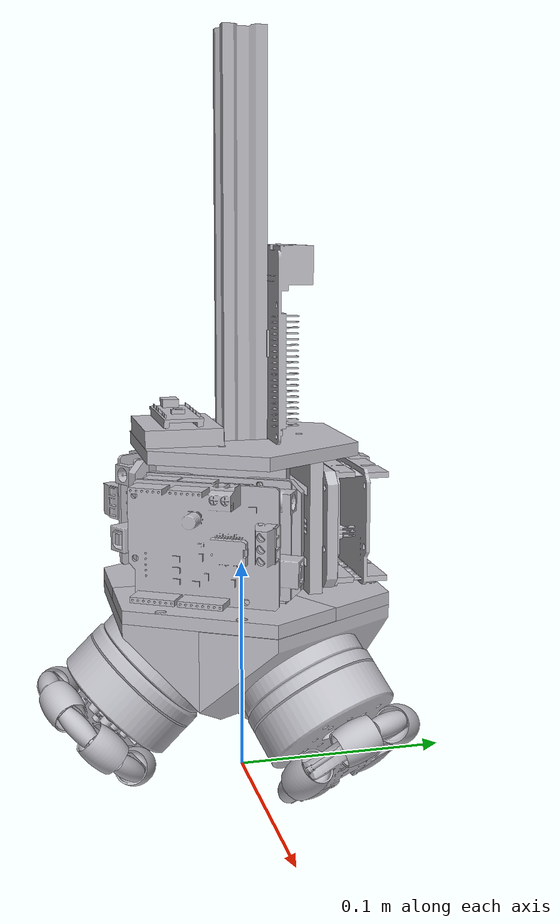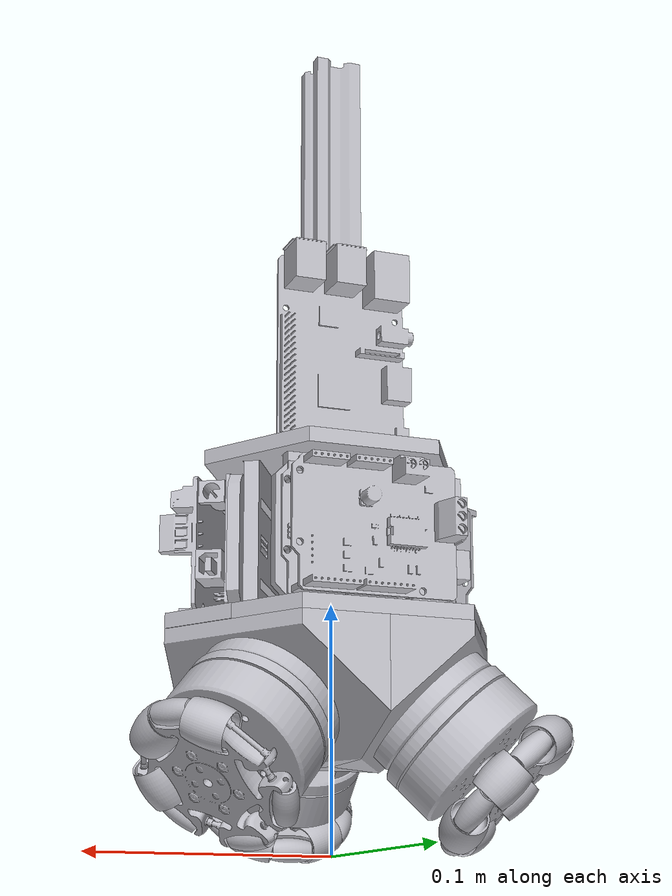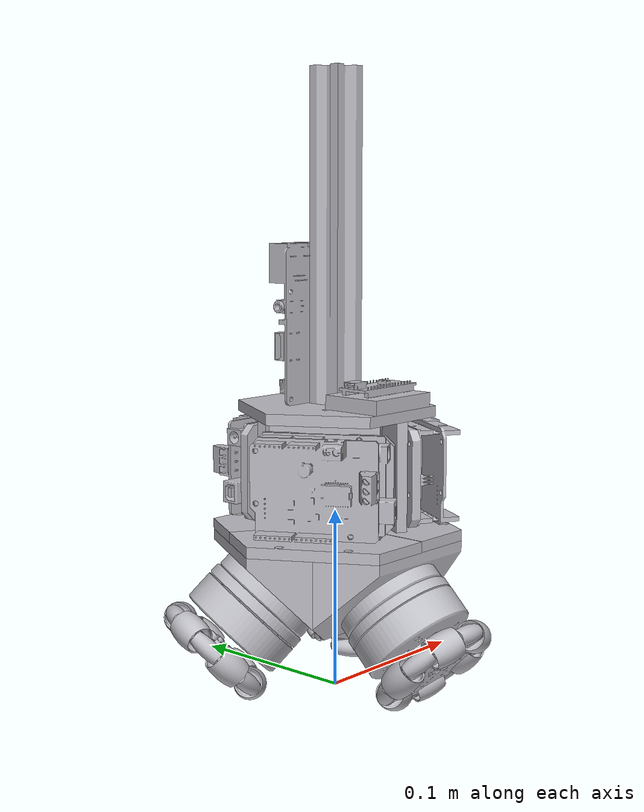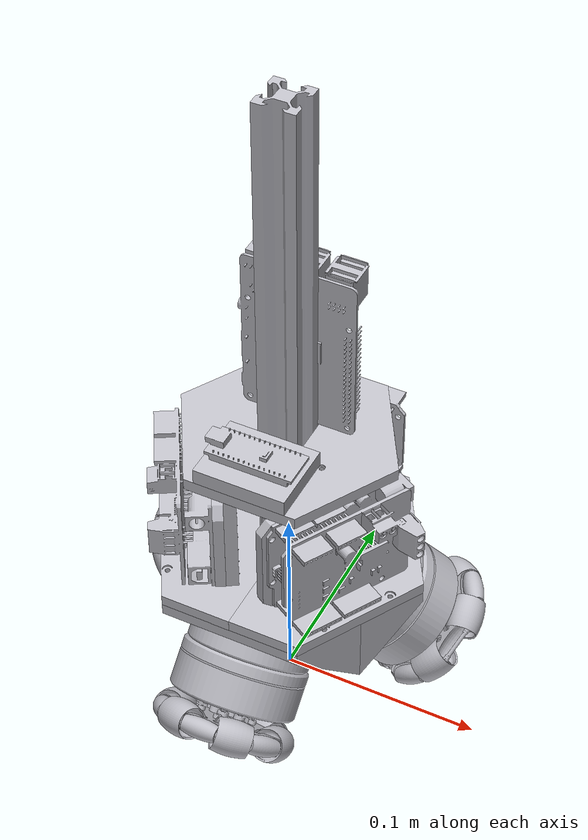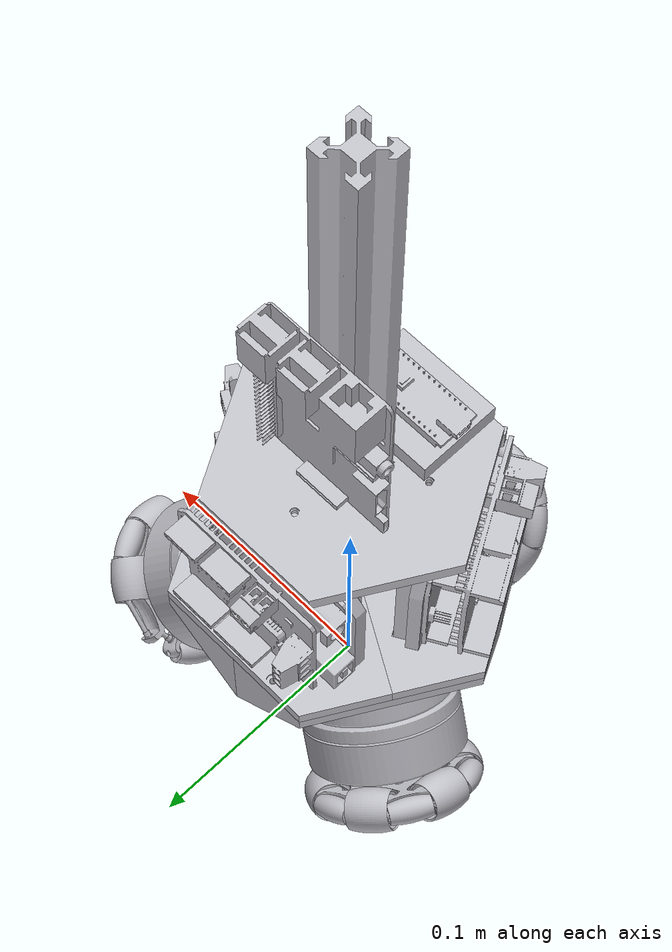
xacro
<?xml version="1.0" ?>
<robot name="deep_ballbot" xmlns:xacro="http://www.ros.org/wiki/xacro">

<xacro:include filename="$(find deep_ballbot)/urdf/materials.xacro" />
<xacro:include filename="$(find deep_ballbot)/urdf/deep_ballbot.trans" />
<xacro:include filename="$(find deep_ballbot)/urdf/deep_ballbot.gazebo" />
<link name="base_link">
  <inertial>
    <origin rpy="0 0 0" xyz="7.650202289024707e-17 7.328088508434192e-16 0.19082500000000008"/>
    <mass value="0.14294070000000003"/>
    <inertia ixx="0.001077" ixy="0.0" ixz="0.0" iyy="0.001077" iyz="-0.0" izz="1.1e-05"/>
  </inertial>
  <visual>
    <origin rpy="0 0 0" xyz="0 0 0"/>
    <geometry>
      <mesh filename="file://$(find deep_ballbot)/meshes/base_link.stl" scale="0.001 0.001 0.001"/>
    </geometry>
    <material name="silver"/>
  </visual>
  <collision>
    <origin rpy="0 0 0" xyz="0 0 0"/>
    <geometry>
      <mesh filename="file://$(find deep_ballbot)/meshes/base_link.stl" scale="0.001 0.001 0.001"/>
    </geometry>
  </collision>
</link>

<link name="base_shell1_1">
  <inertial>
    <origin rpy="0 0 0" xyz="-0.03154930294610876 0.018214998548683293 0.021364464404157145"/>
    <mass value="0.03897424370875782"/>
    <inertia ixx="3.3e-05" ixy="-1.1e-05" ixz="6e-06" iyy="2e-05" iyz="-3e-06" izz="3.8e-05"/>
  </inertial>
  <visual>
    <origin rpy="0 0 0" xyz="-0.0 -0.0 -0.040825"/>
    <geometry>
      <mesh filename="file://$(find deep_ballbot)/meshes/base_shell1_1.stl" scale="0.001 0.001 0.001"/>
    </geometry>
    <material name="silver"/>
  </visual>
  <collision>
    <origin rpy="0 0 0" xyz="-0.0 -0.0 -0.040825"/>
    <geometry>
      <mesh filename="file://$(find deep_ballbot)/meshes/base_shell1_1.stl" scale="0.001 0.001 0.001"/>
    </geometry>
  </collision>
</link>

<link name="base_shell2_1">
  <inertial>
    <origin rpy="0 0 0" xyz="-3.4440123730969962e-15 -0.03702245966743223 0.022039444136548625"/>
    <mass value="0.037632056653399984"/>
    <inertia ixx="1.3e-05" ixy="-0.0" ixz="-0.0" iyy="3.8e-05" iyz="6e-06" izz="3.7e-05"/>
  </inertial>
  <visual>
    <origin rpy="0 0 0" xyz="-0.0 -0.0 -0.040825"/>
    <geometry>
      <mesh filename="file://$(find deep_ballbot)/meshes/base_shell2_1.stl" scale="0.001 0.001 0.001"/>
    </geometry>
    <material name="silver"/>
  </visual>
  <collision>
    <origin rpy="0 0 0" xyz="-0.0 -0.0 -0.040825"/>
    <geometry>
      <mesh filename="file://$(find deep_ballbot)/meshes/base_shell2_1.stl" scale="0.001 0.001 0.001"/>
    </geometry>
  </collision>
</link>

<link name="base_shell3_1">
  <inertial>
    <origin rpy="0 0 0" xyz="0.03154930294610811 0.01821499854867976 0.021364464404157152"/>
    <mass value="0.03897424370875781"/>
    <inertia ixx="3.3e-05" ixy="1.1e-05" ixz="-6e-06" iyy="2e-05" iyz="-3e-06" izz="3.8e-05"/>
  </inertial>
  <visual>
    <origin rpy="0 0 0" xyz="-0.0 -0.0 -0.040825"/>
    <geometry>
      <mesh filename="file://$(find deep_ballbot)/meshes/base_shell3_1.stl" scale="0.001 0.001 0.001"/>
    </geometry>
    <material name="silver"/>
  </visual>
  <collision>
    <origin rpy="0 0 0" xyz="-0.0 -0.0 -0.040825"/>
    <geometry>
      <mesh filename="file://$(find deep_ballbot)/meshes/base_shell3_1.stl" scale="0.001 0.001 0.001"/>
    </geometry>
  </collision>
</link>

<link name="base_plate2_1">
  <inertial>
    <origin rpy="0 0 0" xyz="-0.008447575075313345 0.025970793969406637 0.0029137797806522564"/>
    <mass value="0.02933177510284292"/>
    <inertia ixx="1.5e-05" ixy="-6e-06" ixz="-0.0" iyy="9e-06" iyz="0.0" izz="2.4e-05"/>
  </inertial>
  <visual>
    <origin rpy="0 0 0" xyz="-0.040768 0.044631 -0.085825"/>
    <geometry>
      <mesh filename="file://$(find deep_ballbot)/meshes/base_plate2_1.stl" scale="0.001 0.001 0.001"/>
    </geometry>
    <material name="silver"/>
  </visual>
  <collision>
    <origin rpy="0 0 0" xyz="-0.040768 0.044631 -0.085825"/>
    <geometry>
      <mesh filename="file://$(find deep_ballbot)/meshes/base_plate2_1.stl" scale="0.001 0.001 0.001"/>
    </geometry>
  </collision>
</link>

<link name="base_plate3_1">
  <inertial>
    <origin rpy="0 0 0" xyz="-0.018267999999997113 -0.02030158793881589 0.0029137797806522703"/>
    <mass value="0.029331775102842895"/>
    <inertia ixx="5e-06" ixy="-0.0" ixz="0.0" iyy="1.9e-05" iyz="-0.0" izz="2.4e-05"/>
  </inertial>
  <visual>
    <origin rpy="0 0 0" xyz="-0.018268 -0.057622 -0.085825"/>
    <geometry>
      <mesh filename="file://$(find deep_ballbot)/meshes/base_plate3_1.stl" scale="0.001 0.001 0.001"/>
    </geometry>
    <material name="silver"/>
  </visual>
  <collision>
    <origin rpy="0 0 0" xyz="-0.018268 -0.057622 -0.085825"/>
    <geometry>
      <mesh filename="file://$(find deep_ballbot)/meshes/base_plate3_1.stl" scale="0.001 0.001 0.001"/>
    </geometry>
  </collision>
</link>

<link name="vertical_bay1_1">
  <inertial>
    <origin rpy="0 0 0" xyz="-1.616755785464885e-07 1.1086679645340436e-07 0.034267969497609505"/>
    <mass value="0.026735006528336703"/>
    <inertia ixx="1.7e-05" ixy="4e-06" ixz="0.0" iyy="1.3e-05" iyz="0.0" izz="8e-06"/>
  </inertial>
  <visual>
    <origin rpy="0 0 0" xyz="0.023921 0.013811 -0.088825"/>
    <geometry>
      <mesh filename="file://$(find deep_ballbot)/meshes/vertical_bay1_1.stl" scale="0.001 0.001 0.001"/>
    </geometry>
    <material name="silver"/>
  </visual>
  <collision>
    <origin rpy="0 0 0" xyz="0.023921 0.013811 -0.088825"/>
    <geometry>
      <mesh filename="file://$(find deep_ballbot)/meshes/vertical_bay1_1.stl" scale="0.001 0.001 0.001"/>
    </geometry>
  </collision>
</link>

<link name="vertical_bay2_1">
  <inertial>
    <origin rpy="0 0 0" xyz="1.6167524609367323e-07 1.1086746340080444e-07 0.03430752132988969"/>
    <mass value="0.026769047843990486"/>
    <inertia ixx="1.8e-05" ixy="-4e-06" ixz="0.0" iyy="1.3e-05" iyz="-0.0" izz="8e-06"/>
  </inertial>
  <visual>
    <origin rpy="0 0 0" xyz="-0.023921 0.013811 -0.088825"/>
    <geometry>
      <mesh filename="file://$(find deep_ballbot)/meshes/vertical_bay2_1.stl" scale="0.001 0.001 0.001"/>
    </geometry>
    <material name="silver"/>
  </visual>
  <collision>
    <origin rpy="0 0 0" xyz="-0.023921 0.013811 -0.088825"/>
    <geometry>
      <mesh filename="file://$(find deep_ballbot)/meshes/vertical_bay2_1.stl" scale="0.001 0.001 0.001"/>
    </geometry>
  </collision>
</link>

<link name="vertical_bay3_1">
  <inertial>
    <origin rpy="0 0 0" xyz="4.811851328225059e-15 -2.2173493282803824e-07 0.03430752132988969"/>
    <mass value="0.026769047843990517"/>
    <inertia ixx="1.1e-05" ixy="-0.0" ixz="-0.0" iyy="2e-05" iyz="0.0" izz="8e-06"/>
  </inertial>
  <visual>
    <origin rpy="0 0 0" xyz="-0.0 -0.027622 -0.088825"/>
    <geometry>
      <mesh filename="file://$(find deep_ballbot)/meshes/vertical_bay3_1.stl" scale="0.001 0.001 0.001"/>
    </geometry>
    <material name="silver"/>
  </visual>
  <collision>
    <origin rpy="0 0 0" xyz="-0.0 -0.027622 -0.088825"/>
    <geometry>
      <mesh filename="file://$(find deep_ballbot)/meshes/vertical_bay3_1.stl" scale="0.001 0.001 0.001"/>
    </geometry>
  </collision>
</link>

<link name="breadboard_1">
  <inertial>
    <origin rpy="0 0 0" xyz="-3.512780858557447e-10 0.017499602320884315 0.004000000000000087"/>
    <mass value="0.016254000000000234"/>
    <inertia ixx="2e-06" ixy="-0.0" ixz="0.0" iyy="3e-06" iyz="0.0" izz="4e-06"/>
  </inertial>
  <visual>
    <origin rpy="0 0 0" xyz="0.0 0.047631 -0.159825"/>
    <geometry>
      <mesh filename="file://$(find deep_ballbot)/meshes/breadboard_1.stl" scale="0.001 0.001 0.001"/>
    </geometry>
    <material name="silver"/>
  </visual>
  <collision>
    <origin rpy="0 0 0" xyz="0.0 0.047631 -0.159825"/>
    <geometry>
      <mesh filename="file://$(find deep_ballbot)/meshes/breadboard_1.stl" scale="0.001 0.001 0.001"/>
    </geometry>
  </collision>
</link>

<link name="rasbperry_pi_1">
  <inertial>
    <origin rpy="0 0 0" xyz="-0.0012540090701389846 0.004888830200197087 0.057465472519733274"/>
    <mass value="0.1347216757914446"/>
    <inertia ixx="8.3e-05" ixy="0.0" ixz="-0.0" iyy="0.000118" iyz="-9e-06" izz="4.1e-05"/>
  </inertial>
  <visual>
    <origin rpy="0 0 0" xyz="0.0 -0.0105 -0.159825"/>
    <geometry>
      <mesh filename="file://$(find deep_ballbot)/meshes/rasbperry_pi_1.stl" scale="0.001 0.001 0.001"/>
    </geometry>
    <material name="silver"/>
  </visual>
  <collision>
    <origin rpy="0 0 0" xyz="0.0 -0.0105 -0.159825"/>
    <geometry>
      <mesh filename="file://$(find deep_ballbot)/meshes/rasbperry_pi_1.stl" scale="0.001 0.001 0.001"/>
    </geometry>
  </collision>
</link>

<link name="motor_mount1_1">
  <inertial>
    <origin rpy="0 0 0" xyz="0.008784093083896126 -0.005071216542772053 -0.015759829153902304"/>
    <mass value="0.08608420182582004"/>
    <inertia ixx="3.8e-05" ixy="-9e-06" ixz="1e-05" iyy="2.8e-05" iyz="-6e-06" izz="4.3e-05"/>
  </inertial>
  <visual>
    <origin rpy="0 0 0" xyz="0.046487 -0.026839 -0.072881"/>
    <geometry>
      <mesh filename="file://$(find deep_ballbot)/meshes/motor_mount1_1.stl" scale="0.001 0.001 0.001"/>
    </geometry>
    <material name="silver"/>
  </visual>
  <collision>
    <origin rpy="0 0 0" xyz="0.046487 -0.026839 -0.072881"/>
    <geometry>
      <mesh filename="file://$(find deep_ballbot)/meshes/motor_mount1_1.stl" scale="0.001 0.001 0.001"/>
    </geometry>
  </collision>
</link>

<link name="motor_mount2_1">
  <inertial>
    <origin rpy="0 0 0" xyz="1.275150652894624e-14 0.010142433085668805 -0.015759829153751945"/>
    <mass value="0.08608420182581951"/>
    <inertia ixx="2.3e-05" ixy="0.0" ixz="-0.0" iyy="4.3e-05" iyz="1.1e-05" izz="4.3e-05"/>
  </inertial>
  <visual>
    <origin rpy="0 0 0" xyz="-0.0 0.053678 -0.072881"/>
    <geometry>
      <mesh filename="file://$(find deep_ballbot)/meshes/motor_mount2_1.stl" scale="0.001 0.001 0.001"/>
    </geometry>
    <material name="silver"/>
  </visual>
  <collision>
    <origin rpy="0 0 0" xyz="-0.0 0.053678 -0.072881"/>
    <geometry>
      <mesh filename="file://$(find deep_ballbot)/meshes/motor_mount2_1.stl" scale="0.001 0.001 0.001"/>
    </geometry>
  </collision>
</link>

<link name="motor_mount3_1">
  <inertial>
    <origin rpy="0 0 0" xyz="-0.00878409308391042 -0.005071216542746816 -0.015759829153902033"/>
    <mass value="0.08608420182581976"/>
    <inertia ixx="3.8e-05" ixy="9e-06" ixz="-1e-05" iyy="2.8e-05" iyz="-6e-06" izz="4.3e-05"/>
  </inertial>
  <visual>
    <origin rpy="0 0 0" xyz="-0.046487 -0.026839 -0.072881"/>
    <geometry>
      <mesh filename="file://$(find deep_ballbot)/meshes/motor_mount3_1.stl" scale="0.001 0.001 0.001"/>
    </geometry>
    <material name="silver"/>
  </visual>
  <collision>
    <origin rpy="0 0 0" xyz="-0.046487 -0.026839 -0.072881"/>
    <geometry>
      <mesh filename="file://$(find deep_ballbot)/meshes/motor_mount3_1.stl" scale="0.001 0.001 0.001"/>
    </geometry>
  </collision>
</link>

<link name="arduino_mount1_1">
  <inertial>
    <origin rpy="0 0 0" xyz="-0.001798540360722238 -0.0017781689855501954 -2.1615661864343716e-05"/>
    <mass value="0.023201510107992145"/>
    <inertia ixx="1.3e-05" ixy="5e-06" ixz="-0.0" iyy="8e-06" iyz="0.0" izz="1.2e-05"/>
  </inertial>
  <visual>
    <origin rpy="0 0 0" xyz="0.026519 0.015311 -0.121325"/>
    <geometry>
      <mesh filename="file://$(find deep_ballbot)/meshes/arduino_mount1_1.stl" scale="0.001 0.001 0.001"/>
    </geometry>
    <material name="silver"/>
  </visual>
  <collision>
    <origin rpy="0 0 0" xyz="0.026519 0.015311 -0.121325"/>
    <geometry>
      <mesh filename="file://$(find deep_ballbot)/meshes/arduino_mount1_1.stl" scale="0.001 0.001 0.001"/>
    </geometry>
  </collision>
</link>

<link name="arduino_mount2_1">
  <inertial>
    <origin rpy="0 0 0" xyz="0.002439424651872895 -0.0006681248315035682 -2.1615661864288205e-05"/>
    <mass value="0.023201510107960607"/>
    <inertia ixx="1.3e-05" ixy="-5e-06" ixz="-0.0" iyy="8e-06" iyz="-0.0" izz="1.2e-05"/>
  </inertial>
  <visual>
    <origin rpy="0 0 0" xyz="-0.026519 0.015311 -0.121325"/>
    <geometry>
      <mesh filename="file://$(find deep_ballbot)/meshes/arduino_mount2_1.stl" scale="0.001 0.001 0.001"/>
    </geometry>
    <material name="silver"/>
  </visual>
  <collision>
    <origin rpy="0 0 0" xyz="-0.026519 0.015311 -0.121325"/>
    <geometry>
      <mesh filename="file://$(find deep_ballbot)/meshes/arduino_mount2_1.stl" scale="0.001 0.001 0.001"/>
    </geometry>
  </collision>
</link>

<link name="arduino_mount3_1">
  <inertial>
    <origin rpy="0 0 0" xyz="-0.0006408842911585431 0.0024462938179587064 -2.1615661864468616e-05"/>
    <mass value="0.023201510107976282"/>
    <inertia ixx="5e-06" ixy="0.0" ixz="0.0" iyy="1.6e-05" iyz="0.0" izz="1.2e-05"/>
  </inertial>
  <visual>
    <origin rpy="0 0 0" xyz="-0.0 -0.030622 -0.121325"/>
    <geometry>
      <mesh filename="file://$(find deep_ballbot)/meshes/arduino_mount3_1.stl" scale="0.001 0.001 0.001"/>
    </geometry>
    <material name="silver"/>
  </visual>
  <collision>
    <origin rpy="0 0 0" xyz="-0.0 -0.030622 -0.121325"/>
    <geometry>
      <mesh filename="file://$(find deep_ballbot)/meshes/arduino_mount3_1.stl" scale="0.001 0.001 0.001"/>
    </geometry>
  </collision>
</link>

<link name="arduino1_1">
  <inertial>
    <origin rpy="0 0 0" xyz="0.016669585365093106 -0.03466135538644938 0.008758533737846824"/>
    <mass value="0.0763619336554756"/>
    <inertia ixx="4.9e-05" ixy="1.4e-05" ixz="0.0" iyy="2.9e-05" iyz="-1e-06" izz="3.5e-05"/>
  </inertial>
  <visual>
    <origin rpy="0 0 0" xyz="0.047078 -0.010299 -0.112825"/>
    <geometry>
      <mesh filename="file://$(find deep_ballbot)/meshes/arduino1_1.stl" scale="0.001 0.001 0.001"/>
    </geometry>
    <material name="silver"/>
  </visual>
  <collision>
    <origin rpy="0 0 0" xyz="0.047078 -0.010299 -0.112825"/>
    <geometry>
      <mesh filename="file://$(find deep_ballbot)/meshes/arduino1_1.stl" scale="0.001 0.001 0.001"/>
    </geometry>
  </collision>
</link>

<link name="arduino2_1">
  <inertial>
    <origin rpy="0 0 0" xyz="0.02168262597923832 0.031766718129953825 0.008758533737850696"/>
    <mass value="0.07636193365547614"/>
    <inertia ixx="4.6e-05" ixy="-1.6e-05" ixz="1e-06" iyy="3.2e-05" iyz="1e-06" izz="3.5e-05"/>
  </inertial>
  <visual>
    <origin rpy="0 0 0" xyz="-0.01462 0.04592 -0.112825"/>
    <geometry>
      <mesh filename="file://$(find deep_ballbot)/meshes/arduino2_1.stl" scale="0.001 0.001 0.001"/>
    </geometry>
    <material name="silver"/>
  </visual>
  <collision>
    <origin rpy="0 0 0" xyz="-0.01462 0.04592 -0.112825"/>
    <geometry>
      <mesh filename="file://$(find deep_ballbot)/meshes/arduino2_1.stl" scale="0.001 0.001 0.001"/>
    </geometry>
  </collision>
</link>

<link name="arduino3_1">
  <inertial>
    <origin rpy="0 0 0" xyz="-0.03835221134345001 0.0028936372564978483 0.008758533737797336"/>
    <mass value="0.07636193365547543"/>
    <inertia ixx="2.2e-05" ixy="2e-06" ixz="-1e-06" iyy="5.6e-05" iyz="0.0" izz="3.5e-05"/>
  </inertial>
  <visual>
    <origin rpy="0 0 0" xyz="-0.032458 -0.035622 -0.112825"/>
    <geometry>
      <mesh filename="file://$(find deep_ballbot)/meshes/arduino3_1.stl" scale="0.001 0.001 0.001"/>
    </geometry>
    <material name="silver"/>
  </visual>
  <collision>
    <origin rpy="0 0 0" xyz="-0.032458 -0.035622 -0.112825"/>
    <geometry>
      <mesh filename="file://$(find deep_ballbot)/meshes/arduino3_1.stl" scale="0.001 0.001 0.001"/>
    </geometry>
  </collision>
</link>

<link name="motor_stator1_1">
  <inertial>
    <origin rpy="0 0 0" xyz="0.013066369938677859 -0.007543151268847602 -0.01610588123457557"/>
    <mass value="0.2071891794839975"/>
    <inertia ixx="5.6e-05" ixy="-8e-06" ixz="1.6e-05" iyy="4.7e-05" iyz="-9e-06" izz="6.1e-05"/>
  </inertial>
  <visual>
    <origin rpy="0 0 0" xyz="0.051386 -0.029667 -0.067224"/>
    <geometry>
      <mesh filename="file://$(find deep_ballbot)/meshes/motor_stator1_1.stl" scale="0.001 0.001 0.001"/>
    </geometry>
    <material name="silver"/>
  </visual>
  <collision>
    <origin rpy="0 0 0" xyz="0.051386 -0.029667 -0.067224"/>
    <geometry>
      <mesh filename="file://$(find deep_ballbot)/meshes/motor_stator1_1.stl" scale="0.001 0.001 0.001"/>
    </geometry>
  </collision>
</link>

<link name="motor_stator2_1">
  <inertial>
    <origin rpy="0 0 0" xyz="2.153687944363946e-17 0.015087302537697599 -0.01610588123457512"/>
    <mass value="0.20718917948399732"/>
    <inertia ixx="4.2e-05" ixy="0.0" ixz="-0.0" iyy="6.1e-05" iyz="1.8e-05" izz="6.1e-05"/>
  </inertial>
  <visual>
    <origin rpy="0 0 0" xyz="-0.0 0.059335 -0.067224"/>
    <geometry>
      <mesh filename="file://$(find deep_ballbot)/meshes/motor_stator2_1.stl" scale="0.001 0.001 0.001"/>
    </geometry>
    <material name="silver"/>
  </visual>
  <collision>
    <origin rpy="0 0 0" xyz="-0.0 0.059335 -0.067224"/>
    <geometry>
      <mesh filename="file://$(find deep_ballbot)/meshes/motor_stator2_1.stl" scale="0.001 0.001 0.001"/>
    </geometry>
  </collision>
</link>

<link name="motor_stator3_1">
  <inertial>
    <origin rpy="0 0 0" xyz="-0.013066369938677644 -0.007543151268847845 -0.016105881234575542"/>
    <mass value="0.20718917948399762"/>
    <inertia ixx="5.6e-05" ixy="8e-06" ixz="-1.6e-05" iyy="4.7e-05" iyz="-9e-06" izz="6.1e-05"/>
  </inertial>
  <visual>
    <origin rpy="0 0 0" xyz="-0.051386 -0.029667 -0.067224"/>
    <geometry>
      <mesh filename="file://$(find deep_ballbot)/meshes/motor_stator3_1.stl" scale="0.001 0.001 0.001"/>
    </geometry>
    <material name="silver"/>
  </visual>
  <collision>
    <origin rpy="0 0 0" xyz="-0.051386 -0.029667 -0.067224"/>
    <geometry>
      <mesh filename="file://$(find deep_ballbot)/meshes/motor_stator3_1.stl" scale="0.001 0.001 0.001"/>
    </geometry>
  </collision>
</link>

<link name="motor_rotor1_1">
  <inertial>
    <origin rpy="0 0 0" xyz="-0.005759360727442396 0.0033250114622924744 -0.0066512446583098656"/>
    <mass value="0.3781828720603627"/>
    <inertia ixx="0.000136" ixy="-1.9e-05" ixz="3.7e-05" iyy="0.000115" iyz="-2.1e-05" izz="0.000147"/>
  </inertial>
  <visual>
    <origin rpy="0 0 0" xyz="0.041588 -0.024011 -0.047426"/>
    <geometry>
      <mesh filename="file://$(find deep_ballbot)/meshes/motor_rotor1_1.stl" scale="0.001 0.001 0.001"/>
    </geometry>
    <material name="silver"/>
  </visual>
  <collision>
    <origin rpy="0 0 0" xyz="0.041588 -0.024011 -0.047426"/>
    <geometry>
      <mesh filename="file://$(find deep_ballbot)/meshes/motor_rotor1_1.stl" scale="0.001 0.001 0.001"/>
    </geometry>
  </collision>
</link>

<link name="motor_rotor2_1">
  <inertial>
    <origin rpy="0 0 0" xyz="-7.656656279926752e-13 -0.006651022923255909 -0.0066512446583099"/>
    <mass value="0.3781828720603624"/>
    <inertia ixx="0.000104" ixy="-0.0" ixz="-0.0" iyy="0.000147" iyz="4.3e-05" izz="0.000147"/>
  </inertial>
  <visual>
    <origin rpy="0 0 0" xyz="-0.0 0.048021 -0.047426"/>
    <geometry>
      <mesh filename="file://$(find deep_ballbot)/meshes/motor_rotor2_1.stl" scale="0.001 0.001 0.001"/>
    </geometry>
    <material name="silver"/>
  </visual>
  <collision>
    <origin rpy="0 0 0" xyz="-0.0 0.048021 -0.047426"/>
    <geometry>
      <mesh filename="file://$(find deep_ballbot)/meshes/motor_rotor2_1.stl" scale="0.001 0.001 0.001"/>
    </geometry>
  </collision>
</link>

<link name="motor_rotor3_1">
  <inertial>
    <origin rpy="0 0 0" xyz="0.005759360728208256 0.0033250114609660285 -0.006651244658309859"/>
    <mass value="0.37818287206036283"/>
    <inertia ixx="0.000136" ixy="1.9e-05" ixz="-3.7e-05" iyy="0.000115" iyz="-2.1e-05" izz="0.000147"/>
  </inertial>
  <visual>
    <origin rpy="0 0 0" xyz="-0.041588 -0.024011 -0.047426"/>
    <geometry>
      <mesh filename="file://$(find deep_ballbot)/meshes/motor_rotor3_1.stl" scale="0.001 0.001 0.001"/>
    </geometry>
    <material name="silver"/>
  </visual>
  <collision>
    <origin rpy="0 0 0" xyz="-0.041588 -0.024011 -0.047426"/>
    <geometry>
      <mesh filename="file://$(find deep_ballbot)/meshes/motor_rotor3_1.stl" scale="0.001 0.001 0.001"/>
    </geometry>
  </collision>
</link>

<link name="wheel_body1_1">
  <inertial>
    <origin rpy="0 0 0" xyz="-0.007230828099754477 0.004197926495771144 -0.008396531536062644"/>
    <mass value="0.01711866246905887"/>
    <inertia ixx="4e-06" ixy="-1e-06" ixz="1e-06" iyy="4e-06" iyz="-1e-06" izz="5e-06"/>
  </inertial>
  <visual>
    <origin rpy="0 0 0" xyz="0.05261 -0.030375 -0.034698"/>
    <geometry>
      <mesh filename="file://$(find deep_ballbot)/meshes/wheel_body1_1.stl" scale="0.001 0.001 0.001"/>
    </geometry>
    <material name="silver"/>
  </visual>
  <collision>
    <origin rpy="0 0 0" xyz="0.05261 -0.030375 -0.034698"/>
    <geometry>
      <mesh filename="file://$(find deep_ballbot)/meshes/wheel_body1_1.stl" scale="0.001 0.001 0.001"/>
    </geometry>
  </collision>
</link>

<link name="wheel_body2_1">
  <inertial>
    <origin rpy="0 0 0" xyz="-2.0618457227039384e-05 -0.00836114071082407 -0.008396531491025875"/>
    <mass value="0.017118662593146216"/>
    <inertia ixx="3e-06" ixy="-0.0" ixz="0.0" iyy="5e-06" iyz="2e-06" izz="5e-06"/>
  </inertial>
  <visual>
    <origin rpy="0 0 0" xyz="-0.0 0.060749 -0.034698"/>
    <geometry>
      <mesh filename="file://$(find deep_ballbot)/meshes/wheel_body2_1.stl" scale="0.001 0.001 0.001"/>
    </geometry>
    <material name="silver"/>
  </visual>
  <collision>
    <origin rpy="0 0 0" xyz="-0.0 0.060749 -0.034698"/>
    <geometry>
      <mesh filename="file://$(find deep_ballbot)/meshes/wheel_body2_1.stl" scale="0.001 0.001 0.001"/>
    </geometry>
  </collision>
</link>

<link name="wheel_body3_1">
  <inertial>
    <origin rpy="0 0 0" xyz="0.007251872798830904 0.00416228337410076 -0.008396049445361434"/>
    <mass value="0.017119124264976967"/>
    <inertia ixx="4e-06" ixy="1e-06" ixz="-1e-06" iyy="4e-06" iyz="-1e-06" izz="5e-06"/>
  </inertial>
  <visual>
    <origin rpy="0 0 0" xyz="-0.05261 -0.030375 -0.034698"/>
    <geometry>
      <mesh filename="file://$(find deep_ballbot)/meshes/wheel_body3_1.stl" scale="0.001 0.001 0.001"/>
    </geometry>
    <material name="silver"/>
  </visual>
  <collision>
    <origin rpy="0 0 0" xyz="-0.05261 -0.030375 -0.034698"/>
    <geometry>
      <mesh filename="file://$(find deep_ballbot)/meshes/wheel_body3_1.stl" scale="0.001 0.001 0.001"/>
    </geometry>
  </collision>
</link>

<link name="wheel_roller1_2_1">
  <inertial>
    <origin rpy="0 0 0" xyz="1.1343589567669454e-08 -1.5996360053227576e-07 -4.949366530018762e-07"/>
    <mass value="0.0012011377071081653"/>
    <inertia ixx="0.0" ixy="-0.0" ixz="-0.0" iyy="0.0" iyz="-0.0" izz="0.0"/>
  </inertial>
  <visual>
    <origin rpy="0 0 0" xyz="0.07833 -0.045224 -0.047426"/>
    <geometry>
      <mesh filename="file://$(find deep_ballbot)/meshes/wheel_roller1_2_1.stl" scale="0.001 0.001 0.001"/>
    </geometry>
    <material name="silver"/>
  </visual>
  <collision>
    <origin rpy="0 0 0" xyz="0.07833 -0.045224 -0.047426"/>
    <geometry>
      <mesh filename="file://$(find deep_ballbot)/meshes/wheel_roller1_2_1.stl" scale="0.001 0.001 0.001"/>
    </geometry>
  </collision>
</link>

<link name="wheel_roller1_4_1">
  <inertial>
    <origin rpy="0 0 0" xyz="-0.0001901390157527244 -0.0013906180530564166 -0.0005302442651772127"/>
    <mass value="0.0025623256301060215"/>
    <inertia ixx="0.0" ixy="0.0" ixz="0.0" iyy="0.0" iyz="0.0" izz="0.0"/>
  </inertial>
  <visual>
    <origin rpy="0 0 0" xyz="0.080246 -0.032725 -0.042835"/>
    <geometry>
      <mesh filename="file://$(find deep_ballbot)/meshes/wheel_roller1_4_1.stl" scale="0.001 0.001 0.001"/>
    </geometry>
    <material name="silver"/>
  </visual>
  <collision>
    <origin rpy="0 0 0" xyz="0.080246 -0.032725 -0.042835"/>
    <geometry>
      <mesh filename="file://$(find deep_ballbot)/meshes/wheel_roller1_4_1.stl" scale="0.001 0.001 0.001"/>
    </geometry>
  </collision>
</link>

<link name="wheel_roller1_9_1">
  <inertial>
    <origin rpy="0 0 0" xyz="2.168223533494107e-07 -4.6082259186688845e-07 -9.665432621625003e-08"/>
    <mass value="0.0012011377071081348"/>
    <inertia ixx="0.0" ixy="0.0" ixz="0.0" iyy="0.0" iyz="-0.0" izz="0.0"/>
  </inertial>
  <visual>
    <origin rpy="0 0 0" xyz="0.082135 -0.017421 -0.036819"/>
    <geometry>
      <mesh filename="file://$(find deep_ballbot)/meshes/wheel_roller1_9_1.stl" scale="0.001 0.001 0.001"/>
    </geometry>
    <material name="silver"/>
  </visual>
  <collision>
    <origin rpy="0 0 0" xyz="0.082135 -0.017421 -0.036819"/>
    <geometry>
      <mesh filename="file://$(find deep_ballbot)/meshes/wheel_roller1_9_1.stl" scale="0.001 0.001 0.001"/>
    </geometry>
  </collision>
</link>

<link name="wheel_roller1_7_1">
  <inertial>
    <origin rpy="0 0 0" xyz="1.844145551960219e-07 7.146925419185268e-08 3.016277917294863e-07"/>
    <mass value="0.0025623256301059855"/>
    <inertia ixx="0.0" ixy="-0.0" ixz="-0.0" iyy="0.0" iyz="0.0" izz="0.0"/>
  </inertial>
  <visual>
    <origin rpy="0 0 0" xyz="0.073084 -0.011884 -0.026212"/>
    <geometry>
      <mesh filename="file://$(find deep_ballbot)/meshes/wheel_roller1_7_1.stl" scale="0.001 0.001 0.001"/>
    </geometry>
    <material name="silver"/>
  </visual>
  <collision>
    <origin rpy="0 0 0" xyz="0.073084 -0.011884 -0.026212"/>
    <geometry>
      <mesh filename="file://$(find deep_ballbot)/meshes/wheel_roller1_7_1.stl" scale="0.001 0.001 0.001"/>
    </geometry>
  </collision>
</link>

<link name="wheel_roller1_12_1">
  <inertial>
    <origin rpy="0 0 0" xyz="-4.1340771209097404e-07 -3.308052069104714e-07 -1.763657350890846e-07"/>
    <mass value="0.0012011377071081519"/>
    <inertia ixx="0.0" ixy="-0.0" ixz="0.0" iyy="0.0" iyz="0.0" izz="0.0"/>
  </inertial>
  <visual>
    <origin rpy="0 0 0" xyz="0.063771 -0.006813 -0.015612"/>
    <geometry>
      <mesh filename="file://$(find deep_ballbot)/meshes/wheel_roller1_12_1.stl" scale="0.001 0.001 0.001"/>
    </geometry>
    <material name="silver"/>
  </visual>
  <collision>
    <origin rpy="0 0 0" xyz="0.063771 -0.006813 -0.015612"/>
    <geometry>
      <mesh filename="file://$(find deep_ballbot)/meshes/wheel_roller1_12_1.stl" scale="0.001 0.001 0.001"/>
    </geometry>
  </collision>
</link>

<link name="wheel_roller1_5_1">
  <inertial>
    <origin rpy="0 0 0" xyz="4.57179928789464e-07 -4.6555762324602956e-07 6.072472028342824e-08"/>
    <mass value="0.002562325630106018"/>
    <inertia ixx="0.0" ixy="0.0" ixz="-0.0" iyy="0.0" iyz="-0.0" izz="0.0"/>
  </inertial>
  <visual>
    <origin rpy="0 0 0" xyz="0.052608 -0.015208 -0.010141"/>
    <geometry>
      <mesh filename="file://$(find deep_ballbot)/meshes/wheel_roller1_5_1.stl" scale="0.001 0.001 0.001"/>
    </geometry>
    <material name="silver"/>
  </visual>
  <collision>
    <origin rpy="0 0 0" xyz="0.052608 -0.015208 -0.010141"/>
    <geometry>
      <mesh filename="file://$(find deep_ballbot)/meshes/wheel_roller1_5_1.stl" scale="0.001 0.001 0.001"/>
    </geometry>
  </collision>
</link>

<link name="wheel_roller1_10_1">
  <inertial>
    <origin rpy="0 0 0" xyz="3.574854795657112e-07 -3.633992790331997e-07 9.819223634015273e-08"/>
    <mass value="0.0012011377071081634"/>
    <inertia ixx="0.0" ixy="-0.0" ixz="0.0" iyy="0.0" iyz="0.0" izz="0.0"/>
  </inertial>
  <visual>
    <origin rpy="0 0 0" xyz="0.041588 -0.024011 -0.004999"/>
    <geometry>
      <mesh filename="file://$(find deep_ballbot)/meshes/wheel_roller1_10_1.stl" scale="0.001 0.001 0.001"/>
    </geometry>
    <material name="silver"/>
  </visual>
  <collision>
    <origin rpy="0 0 0" xyz="0.041588 -0.024011 -0.004999"/>
    <geometry>
      <mesh filename="file://$(find deep_ballbot)/meshes/wheel_roller1_10_1.stl" scale="0.001 0.001 0.001"/>
    </geometry>
  </collision>
</link>

<link name="wheel_roller1_6_1">
  <inertial>
    <origin rpy="0 0 0" xyz="-1.5083097658352695e-07 4.3352494352721926e-07 -4.748097093606324e-07"/>
    <mass value="0.0025623256301060093"/>
    <inertia ixx="0.0" ixy="0.0" ixz="0.0" iyy="0.0" iyz="0.0" izz="0.0"/>
  </inertial>
  <visual>
    <origin rpy="0 0 0" xyz="0.039475 -0.037946 -0.010138"/>
    <geometry>
      <mesh filename="file://$(find deep_ballbot)/meshes/wheel_roller1_6_1.stl" scale="0.001 0.001 0.001"/>
    </geometry>
    <material name="silver"/>
  </visual>
  <collision>
    <origin rpy="0 0 0" xyz="0.039475 -0.037946 -0.010138"/>
    <geometry>
      <mesh filename="file://$(find deep_ballbot)/meshes/wheel_roller1_6_1.stl" scale="0.001 0.001 0.001"/>
    </geometry>
  </collision>
</link>

<link name="wheel_roller1_11_1">
  <inertial>
    <origin rpy="0 0 0" xyz="1.5200671603377014e-07 -6.25402882536985e-08 -3.000900884626845e-07"/>
    <mass value="0.0012011377071081484"/>
    <inertia ixx="0.0" ixy="0.0" ixz="0.0" iyy="0.0" iyz="-0.0" izz="0.0"/>
  </inertial>
  <visual>
    <origin rpy="0 0 0" xyz="0.037783 -0.051814 -0.015606"/>
    <geometry>
      <mesh filename="file://$(find deep_ballbot)/meshes/wheel_roller1_11_1.stl" scale="0.001 0.001 0.001"/>
    </geometry>
    <material name="silver"/>
  </visual>
  <collision>
    <origin rpy="0 0 0" xyz="0.037783 -0.051814 -0.015606"/>
    <geometry>
      <mesh filename="file://$(find deep_ballbot)/meshes/wheel_roller1_11_1.stl" scale="0.001 0.001 0.001"/>
    </geometry>
  </collision>
</link>

<link name="wheel_roller1_3_1">
  <inertial>
    <origin rpy="0 0 0" xyz="1.844145140969533e-07 4.051678663199998e-07 3.016277917988752e-07"/>
    <mass value="0.002562325630105992"/>
    <inertia ixx="0.0" ixy="-0.0" ixz="-0.0" iyy="0.0" iyz="0.0" izz="0.0"/>
  </inertial>
  <visual>
    <origin rpy="0 0 0" xyz="0.046834 -0.05735 -0.026212"/>
    <geometry>
      <mesh filename="file://$(find deep_ballbot)/meshes/wheel_roller1_3_1.stl" scale="0.001 0.001 0.001"/>
    </geometry>
    <material name="silver"/>
  </visual>
  <collision>
    <origin rpy="0 0 0" xyz="0.046834 -0.05735 -0.026212"/>
    <geometry>
      <mesh filename="file://$(find deep_ballbot)/meshes/wheel_roller1_3_1.stl" scale="0.001 0.001 0.001"/>
    </geometry>
  </collision>
</link>

<link name="wheel_roller1_8_1">
  <inertial>
    <origin rpy="0 0 0" xyz="-2.1064077822263716e-08 -4.608225134400401e-07 -9.66543238570261e-08"/>
    <mass value="0.0012011377071081556"/>
    <inertia ixx="0.0" ixy="-0.0" ixz="0.0" iyy="0.0" iyz="0.0" izz="0.0"/>
  </inertial>
  <visual>
    <origin rpy="0 0 0" xyz="0.056154 -0.062421 -0.036819"/>
    <geometry>
      <mesh filename="file://$(find deep_ballbot)/meshes/wheel_roller1_8_1.stl" scale="0.001 0.001 0.001"/>
    </geometry>
    <material name="silver"/>
  </visual>
  <collision>
    <origin rpy="0 0 0" xyz="0.056154 -0.062421 -0.036819"/>
    <geometry>
      <mesh filename="file://$(find deep_ballbot)/meshes/wheel_roller1_8_1.stl" scale="0.001 0.001 0.001"/>
    </geometry>
  </collision>
</link>

<link name="wheel_roller1_1_1">
  <inertial>
    <origin rpy="0 0 0" xyz="-4.80340058631179e-07 2.0996169394077446e-07 7.806477175797966e-08"/>
    <mass value="0.002562325630106023"/>
    <inertia ixx="0.0" ixy="0.0" ixz="-0.0" iyy="0.0" iyz="-0.0" izz="0.0"/>
  </inertial>
  <visual>
    <origin rpy="0 0 0" xyz="0.067317 -0.054021 -0.042287"/>
    <geometry>
      <mesh filename="file://$(find deep_ballbot)/meshes/wheel_roller1_1_1.stl" scale="0.001 0.001 0.001"/>
    </geometry>
    <material name="silver"/>
  </visual>
  <collision>
    <origin rpy="0 0 0" xyz="0.067317 -0.054021 -0.042287"/>
    <geometry>
      <mesh filename="file://$(find deep_ballbot)/meshes/wheel_roller1_1_1.stl" scale="0.001 0.001 0.001"/>
    </geometry>
  </collision>
</link>

<link name="wheel_roller2_2_1">
  <inertial>
    <origin rpy="0 0 0" xyz="-7.154155730642704e-18 3.19927326214442e-07 -4.949365296977315e-07"/>
    <mass value="0.0012011377071081363"/>
    <inertia ixx="0.0" ixy="-0.0" ixz="0.0" iyy="0.0" iyz="-0.0" izz="0.0"/>
  </inertial>
  <visual>
    <origin rpy="0 0 0" xyz="-0.0 0.090448 -0.047426"/>
    <geometry>
      <mesh filename="file://$(find deep_ballbot)/meshes/wheel_roller2_2_1.stl" scale="0.001 0.001 0.001"/>
    </geometry>
    <material name="silver"/>
  </visual>
  <collision>
    <origin rpy="0 0 0" xyz="-0.0 0.090448 -0.047426"/>
    <geometry>
      <mesh filename="file://$(find deep_ballbot)/meshes/wheel_roller2_2_1.stl" scale="0.001 0.001 0.001"/>
    </geometry>
  </collision>
</link>

<link name="wheel_roller2_4_1">
  <inertial>
    <origin rpy="0 0 0" xyz="0.0012986987297723667 0.0005300692565428089 -0.0005302442653455225"/>
    <mass value="0.002562325630106008"/>
    <inertia ixx="0.0" ixy="0.0" ixz="-0.0" iyy="0.0" iyz="-0.0" izz="0.0"/>
  </inertial>
  <visual>
    <origin rpy="0 0 0" xyz="-0.011783 0.085857 -0.042835"/>
    <geometry>
      <mesh filename="file://$(find deep_ballbot)/meshes/wheel_roller2_4_1.stl" scale="0.001 0.001 0.001"/>
    </geometry>
    <material name="silver"/>
  </visual>
  <collision>
    <origin rpy="0 0 0" xyz="-0.011783 0.085857 -0.042835"/>
    <geometry>
      <mesh filename="file://$(find deep_ballbot)/meshes/wheel_roller2_4_1.stl" scale="0.001 0.001 0.001"/>
    </geometry>
  </collision>
</link>

<link name="wheel_roller2_7_1">
  <inertial>
    <origin rpy="0 0 0" xyz="-2.3788655158923921e-07 -7.835488065321972e-08 -9.665444332396245e-08"/>
    <mass value="0.0012011377071081703"/>
    <inertia ixx="0.0" ixy="-0.0" ixz="0.0" iyy="0.0" iyz="0.0" izz="0.0"/>
  </inertial>
  <visual>
    <origin rpy="0 0 0" xyz="-0.025981 0.079841 -0.036819"/>
    <geometry>
      <mesh filename="file://$(find deep_ballbot)/meshes/wheel_roller2_7_1.stl" scale="0.001 0.001 0.001"/>
    </geometry>
    <material name="silver"/>
  </visual>
  <collision>
    <origin rpy="0 0 0" xyz="-0.025981 0.079841 -0.036819"/>
    <geometry>
      <mesh filename="file://$(find deep_ballbot)/meshes/wheel_roller2_7_1.stl" scale="0.001 0.001 0.001"/>
    </geometry>
  </collision>
</link>

<link name="wheel_roller2_12_1">
  <inertial>
    <origin rpy="0 0 0" xyz="-4.10851908050347e-14 -4.766371183989593e-07 3.016277918058141e-07"/>
    <mass value="0.002562325630106001"/>
    <inertia ixx="0.0" ixy="-0.0" ixz="0.0" iyy="0.0" iyz="-0.0" izz="0.0"/>
  </inertial>
  <visual>
    <origin rpy="0 0 0" xyz="-0.02625 0.069234 -0.026212"/>
    <geometry>
      <mesh filename="file://$(find deep_ballbot)/meshes/wheel_roller2_12_1.stl" scale="0.001 0.001 0.001"/>
    </geometry>
    <material name="silver"/>
  </visual>
  <collision>
    <origin rpy="0 0 0" xyz="-0.02625 0.069234 -0.026212"/>
    <geometry>
      <mesh filename="file://$(find deep_ballbot)/meshes/wheel_roller2_12_1.stl" scale="0.001 0.001 0.001"/>
    </geometry>
  </collision>
</link>

<link name="wheel_roller2_9_1">
  <inertial>
    <origin rpy="0 0 0" xyz="-2.378865543301023e-07 1.3562872630545897e-09 -1.7636561509652704e-07"/>
    <mass value="0.0012011377071081686"/>
    <inertia ixx="0.0" ixy="0.0" ixz="-0.0" iyy="0.0" iyz="0.0" izz="0.0"/>
  </inertial>
  <visual>
    <origin rpy="0 0 0" xyz="-0.025986 0.058634 -0.015612"/>
    <geometry>
      <mesh filename="file://$(find deep_ballbot)/meshes/wheel_roller2_9_1.stl" scale="0.001 0.001 0.001"/>
    </geometry>
    <material name="silver"/>
  </visual>
  <collision>
    <origin rpy="0 0 0" xyz="-0.025986 0.058634 -0.015612"/>
    <geometry>
      <mesh filename="file://$(find deep_ballbot)/meshes/wheel_roller2_9_1.stl" scale="0.001 0.001 0.001"/>
    </geometry>
  </collision>
</link>

<link name="wheel_roller2_5_1">
  <inertial>
    <origin rpy="0 0 0" xyz="-3.3974599703348596e-07 -2.3573421611966516e-07 6.072436503634648e-08"/>
    <mass value="0.0025623256301060045"/>
    <inertia ixx="0.0" ixy="-0.0" ixz="0.0" iyy="0.0" iyz="-0.0" izz="0.0"/>
  </inertial>
  <visual>
    <origin rpy="0 0 0" xyz="-0.013134 0.053163 -0.010141"/>
    <geometry>
      <mesh filename="file://$(find deep_ballbot)/meshes/wheel_roller2_5_1.stl" scale="0.001 0.001 0.001"/>
    </geometry>
    <material name="silver"/>
  </visual>
  <collision>
    <origin rpy="0 0 0" xyz="-0.013134 0.053163 -0.010141"/>
    <geometry>
      <mesh filename="file://$(find deep_ballbot)/meshes/wheel_roller2_5_1.stl" scale="0.001 0.001 0.001"/>
    </geometry>
  </collision>
</link>

<link name="wheel_roller2_10_1">
  <inertial>
    <origin rpy="0 0 0" xyz="-1.3354424030533122e-16 -2.732015630807494e-07 9.819211308631504e-08"/>
    <mass value="0.0012011377071081296"/>
    <inertia ixx="0.0" ixy="0.0" ixz="-0.0" iyy="0.0" iyz="-0.0" izz="0.0"/>
  </inertial>
  <visual>
    <origin rpy="0 0 0" xyz="-0.0 0.048021 -0.004999"/>
    <geometry>
      <mesh filename="file://$(find deep_ballbot)/meshes/wheel_roller2_10_1.stl" scale="0.001 0.001 0.001"/>
    </geometry>
    <material name="silver"/>
  </visual>
  <collision>
    <origin rpy="0 0 0" xyz="-0.0 0.048021 -0.004999"/>
    <geometry>
      <mesh filename="file://$(find deep_ballbot)/meshes/wheel_roller2_10_1.stl" scale="0.001 0.001 0.001"/>
    </geometry>
  </collision>
</link>

<link name="wheel_roller2_6_1">
  <inertial>
    <origin rpy="0 0 0" xyz="3.685073080017531e-14 2.997996893031041e-07 -4.7480954054775204e-07"/>
    <mass value="0.002562325630106014"/>
    <inertia ixx="0.0" ixy="0.0" ixz="-0.0" iyy="0.0" iyz="-0.0" izz="0.0"/>
  </inertial>
  <visual>
    <origin rpy="0 0 0" xyz="0.013125 0.05316 -0.010138"/>
    <geometry>
      <mesh filename="file://$(find deep_ballbot)/meshes/wheel_roller2_6_1.stl" scale="0.001 0.001 0.001"/>
    </geometry>
    <material name="silver"/>
  </visual>
  <collision>
    <origin rpy="0 0 0" xyz="0.013125 0.05316 -0.010138"/>
    <geometry>
      <mesh filename="file://$(find deep_ballbot)/meshes/wheel_roller2_6_1.stl" scale="0.001 0.001 0.001"/>
    </geometry>
  </collision>
</link>

<link name="wheel_roller2_11_1">
  <inertial>
    <origin rpy="0 0 0" xyz="2.3788655255027602e-07 1.2508064517469109e-07 -3.0008997087965783e-07"/>
    <mass value="0.0012011377071081773"/>
    <inertia ixx="0.0" ixy="-0.0" ixz="0.0" iyy="0.0" iyz="0.0" izz="0.0"/>
  </inertial>
  <visual>
    <origin rpy="0 0 0" xyz="0.025981 0.058628 -0.015606"/>
    <geometry>
      <mesh filename="file://$(find deep_ballbot)/meshes/wheel_roller2_11_1.stl" scale="0.001 0.001 0.001"/>
    </geometry>
    <material name="silver"/>
  </visual>
  <collision>
    <origin rpy="0 0 0" xyz="0.025981 0.058628 -0.015606"/>
    <geometry>
      <mesh filename="file://$(find deep_ballbot)/meshes/wheel_roller2_11_1.stl" scale="0.001 0.001 0.001"/>
    </geometry>
  </collision>
</link>

<link name="wheel_roller2_3_1">
  <inertial>
    <origin rpy="0 0 0" xyz="4.114070195626596e-14 -4.766371192871377e-07 3.0162779236092563e-07"/>
    <mass value="0.002562325630106015"/>
    <inertia ixx="0.0" ixy="0.0" ixz="-0.0" iyy="0.0" iyz="-0.0" izz="0.0"/>
  </inertial>
  <visual>
    <origin rpy="0 0 0" xyz="0.02625 0.069234 -0.026212"/>
    <geometry>
      <mesh filename="file://$(find deep_ballbot)/meshes/wheel_roller2_3_1.stl" scale="0.001 0.001 0.001"/>
    </geometry>
    <material name="silver"/>
  </visual>
  <collision>
    <origin rpy="0 0 0" xyz="0.02625 0.069234 -0.026212"/>
    <geometry>
      <mesh filename="file://$(find deep_ballbot)/meshes/wheel_roller2_3_1.stl" scale="0.001 0.001 0.001"/>
    </geometry>
  </collision>
</link>

<link name="wheel_roller2_8_1">
  <inertial>
    <origin rpy="0 0 0" xyz="2.378865539900965e-07 -7.83548799870859e-08 -9.665444396234069e-08"/>
    <mass value="0.0012011377071081415"/>
    <inertia ixx="0.0" ixy="0.0" ixz="-0.0" iyy="0.0" iyz="0.0" izz="0.0"/>
  </inertial>
  <visual>
    <origin rpy="0 0 0" xyz="0.025981 0.079841 -0.036819"/>
    <geometry>
      <mesh filename="file://$(find deep_ballbot)/meshes/wheel_roller2_8_1.stl" scale="0.001 0.001 0.001"/>
    </geometry>
    <material name="silver"/>
  </visual>
  <collision>
    <origin rpy="0 0 0" xyz="0.025981 0.079841 -0.036819"/>
    <geometry>
      <mesh filename="file://$(find deep_ballbot)/meshes/wheel_roller2_8_1.stl" scale="0.001 0.001 0.001"/>
    </geometry>
  </collision>
</link>

<link name="wheel_roller2_1_1">
  <inertial>
    <origin rpy="0 0 0" xyz="3.802513859341161e-14 -2.530739275363736e-07 7.806512464930693e-08"/>
    <mass value="0.002562325630106016"/>
    <inertia ixx="0.0" ixy="-0.0" ixz="0.0" iyy="0.0" iyz="-0.0" izz="0.0"/>
  </inertial>
  <visual>
    <origin rpy="0 0 0" xyz="0.013125 0.085309 -0.042287"/>
    <geometry>
      <mesh filename="file://$(find deep_ballbot)/meshes/wheel_roller2_1_1.stl" scale="0.001 0.001 0.001"/>
    </geometry>
    <material name="silver"/>
  </visual>
  <collision>
    <origin rpy="0 0 0" xyz="0.013125 0.085309 -0.042287"/>
    <geometry>
      <mesh filename="file://$(find deep_ballbot)/meshes/wheel_roller2_1_1.stl" scale="0.001 0.001 0.001"/>
    </geometry>
  </collision>
</link>

<link name="wheel_roller3_2_1">
  <inertial>
    <origin rpy="0 0 0" xyz="-1.1343589581547242e-08 -1.5996360108044838e-07 -4.949366529324872e-07"/>
    <mass value="0.0012011377071081515"/>
    <inertia ixx="0.0" ixy="0.0" ixz="0.0" iyy="0.0" iyz="0.0" izz="0.0"/>
  </inertial>
  <visual>
    <origin rpy="0 0 0" xyz="-0.07833 -0.045224 -0.047426"/>
    <geometry>
      <mesh filename="file://$(find deep_ballbot)/meshes/wheel_roller3_2_1.stl" scale="0.001 0.001 0.001"/>
    </geometry>
    <material name="silver"/>
  </visual>
  <collision>
    <origin rpy="0 0 0" xyz="-0.07833 -0.045224 -0.047426"/>
    <geometry>
      <mesh filename="file://$(find deep_ballbot)/meshes/wheel_roller3_2_1.stl" scale="0.001 0.001 0.001"/>
    </geometry>
  </collision>
</link>

<link name="wheel_roller3_4_1">
  <inertial>
    <origin rpy="0 0 0" xyz="-0.0011085597139543352 0.0008595487964584703 -0.000530244265698844"/>
    <mass value="0.0025623256301060124"/>
    <inertia ixx="0.0" ixy="-0.0" ixz="0.0" iyy="0.0" iyz="-0.0" izz="0.0"/>
  </inertial>
  <visual>
    <origin rpy="0 0 0" xyz="-0.068463 -0.053133 -0.042835"/>
    <geometry>
      <mesh filename="file://$(find deep_ballbot)/meshes/wheel_roller3_4_1.stl" scale="0.001 0.001 0.001"/>
    </geometry>
    <material name="silver"/>
  </visual>
  <collision>
    <origin rpy="0 0 0" xyz="-0.068463 -0.053133 -0.042835"/>
    <geometry>
      <mesh filename="file://$(find deep_ballbot)/meshes/wheel_roller3_4_1.stl" scale="0.001 0.001 0.001"/>
    </geometry>
  </collision>
</link>

<link name="wheel_roller3_9_1">
  <inertial>
    <origin rpy="0 0 0" xyz="2.1064077142252113e-08 -4.6082251122653295e-07 -9.665432298966437e-08"/>
    <mass value="0.0012011377071081525"/>
    <inertia ixx="0.0" ixy="0.0" ixz="-0.0" iyy="0.0" iyz="0.0" izz="0.0"/>
  </inertial>
  <visual>
    <origin rpy="0 0 0" xyz="-0.056154 -0.062421 -0.036819"/>
    <geometry>
      <mesh filename="file://$(find deep_ballbot)/meshes/wheel_roller3_9_1.stl" scale="0.001 0.001 0.001"/>
    </geometry>
    <material name="silver"/>
  </visual>
  <collision>
    <origin rpy="0 0 0" xyz="-0.056154 -0.062421 -0.036819"/>
    <geometry>
      <mesh filename="file://$(find deep_ballbot)/meshes/wheel_roller3_9_1.stl" scale="0.001 0.001 0.001"/>
    </geometry>
  </collision>
</link>

<link name="wheel_roller3_7_1">
  <inertial>
    <origin rpy="0 0 0" xyz="-1.844145138749087e-07 4.051678657579494e-07 3.016277917364252e-07"/>
    <mass value="0.0025623256301059846"/>
    <inertia ixx="0.0" ixy="0.0" ixz="0.0" iyy="0.0" iyz="0.0" izz="0.0"/>
  </inertial>
  <visual>
    <origin rpy="0 0 0" xyz="-0.046834 -0.05735 -0.026212"/>
    <geometry>
      <mesh filename="file://$(find deep_ballbot)/meshes/wheel_roller3_7_1.stl" scale="0.001 0.001 0.001"/>
    </geometry>
    <material name="silver"/>
  </visual>
  <collision>
    <origin rpy="0 0 0" xyz="-0.046834 -0.05735 -0.026212"/>
    <geometry>
      <mesh filename="file://$(find deep_ballbot)/meshes/wheel_roller3_7_1.stl" scale="0.001 0.001 0.001"/>
    </geometry>
  </collision>
</link>

<link name="wheel_roller3_12_1">
  <inertial>
    <origin rpy="0 0 0" xyz="-3.487058551771005e-07 3.294489083899288e-07 -1.763657322077089e-07"/>
    <mass value="0.0012011377071081436"/>
    <inertia ixx="0.0" ixy="-0.0" ixz="-0.0" iyy="0.0" iyz="-0.0" izz="0.0"/>
  </inertial>
  <visual>
    <origin rpy="0 0 0" xyz="-0.037786 -0.051821 -0.015612"/>
    <geometry>
      <mesh filename="file://$(find deep_ballbot)/meshes/wheel_roller3_12_1.stl" scale="0.001 0.001 0.001"/>
    </geometry>
    <material name="silver"/>
  </visual>
  <collision>
    <origin rpy="0 0 0" xyz="-0.037786 -0.051821 -0.015612"/>
    <geometry>
      <mesh filename="file://$(find deep_ballbot)/meshes/wheel_roller3_12_1.stl" scale="0.001 0.001 0.001"/>
    </geometry>
  </collision>
</link>

<link name="wheel_roller3_5_1">
  <inertial>
    <origin rpy="0 0 0" xyz="-1.1743386531953837e-07 -2.987081017744031e-07 6.07241959025423e-08"/>
    <mass value="0.0025623256301060124"/>
    <inertia ixx="0.0" ixy="-0.0" ixz="-0.0" iyy="0.0" iyz="0.0" izz="0.0"/>
  </inertial>
  <visual>
    <origin rpy="0 0 0" xyz="-0.039474 -0.037956 -0.010141"/>
    <geometry>
      <mesh filename="file://$(find deep_ballbot)/meshes/wheel_roller3_5_1.stl" scale="0.001 0.001 0.001"/>
    </geometry>
    <material name="silver"/>
  </visual>
  <collision>
    <origin rpy="0 0 0" xyz="-0.039474 -0.037956 -0.010141"/>
    <geometry>
      <mesh filename="file://$(find deep_ballbot)/meshes/wheel_roller3_5_1.stl" scale="0.001 0.001 0.001"/>
    </geometry>
  </collision>
</link>

<link name="wheel_roller3_10_1">
  <inertial>
    <origin rpy="0 0 0" xyz="-3.5748547974612244e-07 -3.633992796993335e-07 9.819223630545826e-08"/>
    <mass value="0.0012011377071081627"/>
    <inertia ixx="0.0" ixy="0.0" ixz="-0.0" iyy="0.0" iyz="-0.0" izz="0.0"/>
  </inertial>
  <visual>
    <origin rpy="0 0 0" xyz="-0.041588 -0.024011 -0.004999"/>
    <geometry>
      <mesh filename="file://$(find deep_ballbot)/meshes/wheel_roller3_10_1.stl" scale="0.001 0.001 0.001"/>
    </geometry>
    <material name="silver"/>
  </visual>
  <collision>
    <origin rpy="0 0 0" xyz="-0.041588 -0.024011 -0.004999"/>
    <geometry>
      <mesh filename="file://$(find deep_ballbot)/meshes/wheel_roller3_10_1.stl" scale="0.001 0.001 0.001"/>
    </geometry>
  </collision>
</link>

<link name="wheel_roller3_6_1">
  <inertial>
    <origin rpy="0 0 0" xyz="1.5083087304135212e-07 2.666754259066789e-07 -4.7480918512893266e-07"/>
    <mass value="0.002562325630105982"/>
    <inertia ixx="0.0" ixy="-0.0" ixz="0.0" iyy="0.0" iyz="-0.0" izz="0.0"/>
  </inertial>
  <visual>
    <origin rpy="0 0 0" xyz="-0.0526 -0.015213 -0.010138"/>
    <geometry>
      <mesh filename="file://$(find deep_ballbot)/meshes/wheel_roller3_6_1.stl" scale="0.001 0.001 0.001"/>
    </geometry>
    <material name="silver"/>
  </visual>
  <collision>
    <origin rpy="0 0 0" xyz="-0.0526 -0.015213 -0.010138"/>
    <geometry>
      <mesh filename="file://$(find deep_ballbot)/meshes/wheel_roller3_6_1.stl" scale="0.001 0.001 0.001"/>
    </geometry>
  </collision>
</link>

<link name="wheel_roller3_11_1">
  <inertial>
    <origin rpy="0 0 0" xyz="-3.8989314764259486e-07 -6.254036871451013e-08 -3.0009009135620324e-07"/>
    <mass value="0.00120113770710816"/>
    <inertia ixx="0.0" ixy="0.0" ixz="-0.0" iyy="0.0" iyz="0.0" izz="0.0"/>
  </inertial>
  <visual>
    <origin rpy="0 0 0" xyz="-0.063764 -0.006814 -0.015606"/>
    <geometry>
      <mesh filename="file://$(find deep_ballbot)/meshes/wheel_roller3_11_1.stl" scale="0.001 0.001 0.001"/>
    </geometry>
    <material name="silver"/>
  </visual>
  <collision>
    <origin rpy="0 0 0" xyz="-0.063764 -0.006814 -0.015606"/>
    <geometry>
      <mesh filename="file://$(find deep_ballbot)/meshes/wheel_roller3_11_1.stl" scale="0.001 0.001 0.001"/>
    </geometry>
  </collision>
</link>

<link name="wheel_roller3_3_1">
  <inertial>
    <origin rpy="0 0 0" xyz="-1.8441455491846614e-07 7.146925409297344e-08 3.016277918266308e-07"/>
    <mass value="0.00256232563010598"/>
    <inertia ixx="0.0" ixy="0.0" ixz="0.0" iyy="0.0" iyz="0.0" izz="0.0"/>
  </inertial>
  <visual>
    <origin rpy="0 0 0" xyz="-0.073084 -0.011884 -0.026212"/>
    <geometry>
      <mesh filename="file://$(find deep_ballbot)/meshes/wheel_roller3_3_1.stl" scale="0.001 0.001 0.001"/>
    </geometry>
    <material name="silver"/>
  </visual>
  <collision>
    <origin rpy="0 0 0" xyz="-0.073084 -0.011884 -0.026212"/>
    <geometry>
      <mesh filename="file://$(find deep_ballbot)/meshes/wheel_roller3_3_1.stl" scale="0.001 0.001 0.001"/>
    </geometry>
  </collision>
</link>

<link name="wheel_roller3_8_1">
  <inertial>
    <origin rpy="0 0 0" xyz="-2.1682235522291204e-07 -4.6082259019808447e-07 -9.665432788158457e-08"/>
    <mass value="0.0012011377071081688"/>
    <inertia ixx="0.0" ixy="-0.0" ixz="-0.0" iyy="0.0" iyz="-0.0" izz="0.0"/>
  </inertial>
  <visual>
    <origin rpy="0 0 0" xyz="-0.082135 -0.017421 -0.036819"/>
    <geometry>
      <mesh filename="file://$(find deep_ballbot)/meshes/wheel_roller3_8_1.stl" scale="0.001 0.001 0.001"/>
    </geometry>
    <material name="silver"/>
  </visual>
  <collision>
    <origin rpy="0 0 0" xyz="-0.082135 -0.017421 -0.036819"/>
    <geometry>
      <mesh filename="file://$(find deep_ballbot)/meshes/wheel_roller3_8_1.stl" scale="0.001 0.001 0.001"/>
    </geometry>
  </collision>
</link>

<link name="wheel_roller3_1_1">
  <inertial>
    <origin rpy="0 0 0" xyz="4.803399548530818e-07 4.311217834118697e-08 7.806529294523967e-08"/>
    <mass value="0.002562325630106005"/>
    <inertia ixx="0.0" ixy="-0.0" ixz="-0.0" iyy="0.0" iyz="0.0" izz="0.0"/>
  </inertial>
  <visual>
    <origin rpy="0 0 0" xyz="-0.080442 -0.031288 -0.042287"/>
    <geometry>
      <mesh filename="file://$(find deep_ballbot)/meshes/wheel_roller3_1_1.stl" scale="0.001 0.001 0.001"/>
    </geometry>
    <material name="silver"/>
  </visual>
  <collision>
    <origin rpy="0 0 0" xyz="-0.080442 -0.031288 -0.042287"/>
    <geometry>
      <mesh filename="file://$(find deep_ballbot)/meshes/wheel_roller3_1_1.stl" scale="0.001 0.001 0.001"/>
    </geometry>
  </collision>
</link>

<link name="simplefocshield1_1">
  <inertial>
    <origin rpy="0 0 0" xyz="0.004365878014859034 -0.03836042712338405 0.010354662282568206"/>
    <mass value="0.08735557008432601"/>
    <inertia ixx="4.9e-05" ixy="1.3e-05" ixz="-0.0" iyy="3e-05" iyz="2e-06" izz="3.4e-05"/>
  </inertial>
  <visual>
    <origin rpy="0 0 0" xyz="0.048464 -0.009499 -0.112825"/>
    <geometry>
      <mesh filename="file://$(find deep_ballbot)/meshes/simplefocshield1_1.stl" scale="0.001 0.001 0.001"/>
    </geometry>
    <material name="silver"/>
  </visual>
  <collision>
    <origin rpy="0 0 0" xyz="0.048464 -0.009499 -0.112825"/>
    <geometry>
      <mesh filename="file://$(find deep_ballbot)/meshes/simplefocshield1_1.stl" scale="0.001 0.001 0.001"/>
    </geometry>
  </collision>
</link>

<link name="simplefocshield2_1">
  <inertial>
    <origin rpy="0 0 0" xyz="0.031037790143420597 0.022960619391438227 0.010354662550761673"/>
    <mass value="0.0873555707013886"/>
    <inertia ixx="4.6e-05" ixy="-1.4e-05" ixz="-2e-06" iyy="3.3e-05" iyz="-1e-06" izz="3.4e-05"/>
  </inertial>
  <visual>
    <origin rpy="0 0 0" xyz="-0.016006 0.04672 -0.112825"/>
    <geometry>
      <mesh filename="file://$(find deep_ballbot)/meshes/simplefocshield2_1.stl" scale="0.001 0.001 0.001"/>
    </geometry>
    <material name="silver"/>
  </visual>
  <collision>
    <origin rpy="0 0 0" xyz="-0.016006 0.04672 -0.112825"/>
    <geometry>
      <mesh filename="file://$(find deep_ballbot)/meshes/simplefocshield2_1.stl" scale="0.001 0.001 0.001"/>
    </geometry>
  </collision>
</link>

<link name="simplefocshield3_1">
  <inertial>
    <origin rpy="0 0 0" xyz="-0.03540366842883926 0.015398807516148985 0.010354662395678865"/>
    <mass value="0.0873555728630959"/>
    <inertia ixx="2.4e-05" ixy="2e-06" ixz="2e-06" iyy="5.5e-05" iyz="-1e-06" izz="3.4e-05"/>
  </inertial>
  <visual>
    <origin rpy="0 0 0" xyz="-0.032458 -0.037222 -0.112825"/>
    <geometry>
      <mesh filename="file://$(find deep_ballbot)/meshes/simplefocshield3_1.stl" scale="0.001 0.001 0.001"/>
    </geometry>
    <material name="silver"/>
  </visual>
  <collision>
    <origin rpy="0 0 0" xyz="-0.032458 -0.037222 -0.112825"/>
    <geometry>
      <mesh filename="file://$(find deep_ballbot)/meshes/simplefocshield3_1.stl" scale="0.001 0.001 0.001"/>
    </geometry>
  </collision>
</link>

<link name="base_plate1_1">
  <inertial>
    <origin rpy="0 0 0" xyz="0.026715575075310714 -0.005670206030588534 0.0029137797806522703"/>
    <mass value="0.029331775102842902"/>
    <inertia ixx="1.5e-05" ixy="6e-06" ixz="0.0" iyy="9e-06" iyz="0.0" izz="2.4e-05"/>
  </inertial>
  <visual>
    <origin rpy="0 0 0" xyz="0.059036 0.01299 -0.085825"/>
    <geometry>
      <mesh filename="file://$(find deep_ballbot)/meshes/base_plate1_1.stl" scale="0.001 0.001 0.001"/>
    </geometry>
    <material name="silver"/>
  </visual>
  <collision>
    <origin rpy="0 0 0" xyz="0.059036 0.01299 -0.085825"/>
    <geometry>
      <mesh filename="file://$(find deep_ballbot)/meshes/base_plate1_1.stl" scale="0.001 0.001 0.001"/>
    </geometry>
  </collision>
</link>

<link name="top_plate_1">
  <inertial>
    <origin rpy="0 0 0" xyz="0.023920999358289983 0.013810999483771975 0.0001394387833444921"/>
    <mass value="0.03865794031509111"/>
    <inertia ixx="2.6e-05" ixy="-0.0" ixz="-0.0" iyy="2.6e-05" iyz="-0.0" izz="5.2e-05"/>
  </inertial>
  <visual>
    <origin rpy="0 0 0" xyz="0.023921 0.013811 -0.156825"/>
    <geometry>
      <mesh filename="file://$(find deep_ballbot)/meshes/top_plate_1.stl" scale="0.001 0.001 0.001"/>
    </geometry>
    <material name="silver"/>
  </visual>
  <collision>
    <origin rpy="0 0 0" xyz="0.023921 0.013811 -0.156825"/>
    <geometry>
      <mesh filename="file://$(find deep_ballbot)/meshes/top_plate_1.stl" scale="0.001 0.001 0.001"/>
    </geometry>
  </collision>
</link>

<link name="arduino_nano_1">
  <inertial>
    <origin rpy="0 0 0" xyz="-0.0012402703223249748 -3.976887548752528e-07 0.003855883406889221"/>
    <mass value="0.014605507737955575"/>
    <inertia ixx="1e-06" ixy="-0.0" ixz="0.0" iyy="2e-06" iyz="0.0" izz="3e-06"/>
  </inertial>
  <visual>
    <origin rpy="0 0 0" xyz="0.0 0.030131 -0.167825"/>
    <geometry>
      <mesh filename="file://$(find deep_ballbot)/meshes/arduino_nano_1.stl" scale="0.001 0.001 0.001"/>
    </geometry>
    <material name="silver"/>
  </visual>
  <collision>
    <origin rpy="0 0 0" xyz="0.0 0.030131 -0.167825"/>
    <geometry>
      <mesh filename="file://$(find deep_ballbot)/meshes/arduino_nano_1.stl" scale="0.001 0.001 0.001"/>
    </geometry>
  </collision>
</link>

<joint name="Rigid1" type="fixed">
  <origin rpy="0 0 0" xyz="0.0 0.0 0.040825"/>
  <parent link="base_link"/>
  <child link="base_shell1_1"/>
</joint>

<joint name="Rigid2" type="fixed">
  <origin rpy="0 0 0" xyz="0.0 0.0 0.040825"/>
  <parent link="base_link"/>
  <child link="base_shell2_1"/>
</joint>

<joint name="Rigid3" type="fixed">
  <origin rpy="0 0 0" xyz="0.0 0.0 0.040825"/>
  <parent link="base_link"/>
  <child link="base_shell3_1"/>
</joint>

<joint name="Rigid5" type="fixed">
  <origin rpy="0 0 0" xyz="0.040768 -0.044631 0.045"/>
  <parent link="base_shell2_1"/>
  <child link="base_plate2_1"/>
</joint>

<joint name="Rigid6" type="fixed">
  <origin rpy="0 0 0" xyz="0.018268 0.057622 0.045"/>
  <parent link="base_shell3_1"/>
  <child link="base_plate3_1"/>
</joint>

<joint name="Rigid7" type="fixed">
  <origin rpy="0 0 0" xyz="0.035115 -0.000821 0.003"/>
  <parent link="base_plate1_1"/>
  <child link="vertical_bay1_1"/>
</joint>

<joint name="Rigid8" type="fixed">
  <origin rpy="0 0 0" xyz="-0.016847 0.03082 0.003"/>
  <parent link="base_plate2_1"/>
  <child link="vertical_bay2_1"/>
</joint>

<joint name="Rigid9" type="fixed">
  <origin rpy="0 0 0" xyz="-0.018268 -0.03 0.003"/>
  <parent link="base_plate3_1"/>
  <child link="vertical_bay3_1"/>
</joint>

<joint name="Rigid11" type="fixed">
  <origin rpy="0 0 0" xyz="0.023921 -0.03382 0.003"/>
  <parent link="top_plate_1"/>
  <child link="breadboard_1"/>
</joint>

<joint name="Rigid13" type="fixed">
  <origin rpy="0 0 0" xyz="0.023921 0.024311 0.003"/>
  <parent link="top_plate_1"/>
  <child link="rasbperry_pi_1"/>
</joint>

<joint name="Rigid14" type="fixed">
  <origin rpy="0 0 0" xyz="-0.046487 0.026839 0.032056"/>
  <parent link="base_shell1_1"/>
  <child link="motor_mount1_1"/>
</joint>

<joint name="Rigid15" type="fixed">
  <origin rpy="0 0 0" xyz="0.0 -0.053678 0.032056"/>
  <parent link="base_shell2_1"/>
  <child link="motor_mount2_1"/>
</joint>

<joint name="Rigid16" type="fixed">
  <origin rpy="0 0 0" xyz="0.046487 0.026839 0.032056"/>
  <parent link="base_shell3_1"/>
  <child link="motor_mount3_1"/>
</joint>

<joint name="Rigid17" type="fixed">
  <origin rpy="0 0 0" xyz="-0.002598 -0.0015 0.0325"/>
  <parent link="vertical_bay1_1"/>
  <child link="arduino_mount1_1"/>
</joint>

<joint name="Rigid18" type="fixed">
  <origin rpy="0 0 0" xyz="0.002598 -0.0015 0.0325"/>
  <parent link="vertical_bay2_1"/>
  <child link="arduino_mount2_1"/>
</joint>

<joint name="Rigid19" type="fixed">
  <origin rpy="0 0 0" xyz="0.0 0.003 0.0325"/>
  <parent link="vertical_bay3_1"/>
  <child link="arduino_mount3_1"/>
</joint>

<joint name="Rigid20" type="fixed">
  <origin rpy="0 0 0" xyz="-0.020559 0.02561 -0.0085"/>
  <parent link="arduino_mount1_1"/>
  <child link="arduino1_1"/>
</joint>

<joint name="Rigid21" type="fixed">
  <origin rpy="0 0 0" xyz="-0.011899 -0.030609 -0.0085"/>
  <parent link="arduino_mount2_1"/>
  <child link="arduino2_1"/>
</joint>

<joint name="Rigid22" type="fixed">
  <origin rpy="0 0 0" xyz="0.032458 0.005 -0.0085"/>
  <parent link="arduino_mount3_1"/>
  <child link="arduino3_1"/>
</joint>

<joint name="Rigid23" type="fixed">
  <origin rpy="0 0 0" xyz="-0.004899 0.002828 -0.005657"/>
  <parent link="motor_mount1_1"/>
  <child link="motor_stator1_1"/>
</joint>

<joint name="Rigid24" type="fixed">
  <origin rpy="0 0 0" xyz="0.0 -0.005657 -0.005657"/>
  <parent link="motor_mount2_1"/>
  <child link="motor_stator2_1"/>
</joint>

<joint name="Rigid25" type="fixed">
  <origin rpy="0 0 0" xyz="0.004899 0.002828 -0.005657"/>
  <parent link="motor_mount3_1"/>
  <child link="motor_stator3_1"/>
</joint>

<joint name="MotorJoint1" type="continuous">
  <origin rpy="0 0 0" xyz="0.009798 -0.005656 -0.019798"/>
  <parent link="motor_stator1_1"/>
  <child link="motor_rotor1_1"/>
  <axis xyz="-0.612372 0.353553 -0.707107"/>
</joint>

<joint name="MotorJoint2" type="continuous">
  <origin rpy="0 0 0" xyz="0.0 0.011314 -0.019798"/>
  <parent link="motor_stator2_1"/>
  <child link="motor_rotor2_1"/>
  <axis xyz="0.0 -0.707107 -0.707107"/>
</joint>

<joint name="MotorJoint3" type="continuous">
  <origin rpy="0 0 0" xyz="-0.009798 -0.005656 -0.019798"/>
  <parent link="motor_stator3_1"/>
  <child link="motor_rotor3_1"/>
  <axis xyz="0.612372 0.353553 -0.707107"/>
</joint>

<joint name="Rigid26" type="fixed">
  <origin rpy="0 0 0" xyz="-0.011022 0.006364 -0.012728"/>
  <parent link="motor_rotor1_1"/>
  <child link="wheel_body1_1"/>
</joint>

<joint name="Rigid27" type="fixed">
  <origin rpy="0 0 0" xyz="0.0 -0.012728 -0.012728"/>
  <parent link="motor_rotor2_1"/>
  <child link="wheel_body2_1"/>
</joint>

<joint name="Rigid28" type="fixed">
  <origin rpy="0 0 0" xyz="0.011022 0.006364 -0.012728"/>
  <parent link="motor_rotor3_1"/>
  <child link="wheel_body3_1"/>
</joint>

<joint name="Rev1" type="continuous">
  <origin rpy="0 0 0" xyz="-0.02572 0.014849 0.012728"/>
  <parent link="wheel_body1_1"/>
  <child link="wheel_roller1_2_1"/>
  <axis xyz="0.5 0.866025 0.0"/>
</joint>

<joint name="Rev2" type="continuous">
  <origin rpy="0 0 0" xyz="-0.027636 0.00235 0.008137"/>
  <parent link="wheel_body1_1"/>
  <child link="wheel_roller1_4_1"/>
  <axis xyz="-0.126826 -0.926777 -0.353553"/>
</joint>

<joint name="Rev3" type="continuous">
  <origin rpy="0 0 0" xyz="-0.029525 -0.012954 0.002121"/>
  <parent link="wheel_body1_1"/>
  <child link="wheel_roller1_9_1"/>
  <axis xyz="0.28033 -0.739199 -0.612372"/>
</joint>

<joint name="Rev4" type="continuous">
  <origin rpy="0 0 0" xyz="-0.020474 -0.018491 -0.008486"/>
  <parent link="wheel_body1_1"/>
  <child link="wheel_roller1_7_1"/>
  <axis xyz="0.612372 -0.353553 -0.707107"/>
</joint>

<joint name="Rev5" type="continuous">
  <origin rpy="0 0 0" xyz="-0.011161 -0.023562 -0.019086"/>
  <parent link="wheel_body1_1"/>
  <child link="wheel_roller1_12_1"/>
  <axis xyz="-0.78033 -0.126826 0.612372"/>
</joint>

<joint name="Rev6" type="continuous">
  <origin rpy="0 0 0" xyz="2e-06 -0.015167 -0.024557"/>
  <parent link="wheel_body1_1"/>
  <child link="wheel_roller1_5_1"/>
  <axis xyz="0.739199 0.573223 -0.353553"/>
</joint>

<joint name="Rev7" type="continuous">
  <origin rpy="0 0 0" xyz="0.011022 -0.006364 -0.029699"/>
  <parent link="wheel_body1_1"/>
  <child link="wheel_roller1_10_1"/>
  <axis xyz="-0.5 -0.866025 0.0"/>
</joint>

<joint name="Rev8" type="continuous">
  <origin rpy="0 0 0" xyz="0.013135 0.007571 -0.02456"/>
  <parent link="wheel_body1_1"/>
  <child link="wheel_roller1_6_1"/>
  <axis xyz="-0.126826 -0.926777 -0.353553"/>
</joint>

<joint name="Rev9" type="continuous">
  <origin rpy="0 0 0" xyz="0.014827 0.021439 -0.019092"/>
  <parent link="wheel_body1_1"/>
  <child link="wheel_roller1_11_1"/>
  <axis xyz="0.28033 -0.739199 -0.612372"/>
</joint>

<joint name="Rev10" type="continuous">
  <origin rpy="0 0 0" xyz="0.005776 0.026975 -0.008486"/>
  <parent link="wheel_body1_1"/>
  <child link="wheel_roller1_3_1"/>
  <axis xyz="0.612372 -0.353553 -0.707107"/>
</joint>

<joint name="Rev11" type="continuous">
  <origin rpy="0 0 0" xyz="-0.003544 0.032046 0.002121"/>
  <parent link="wheel_body1_1"/>
  <child link="wheel_roller1_8_1"/>
  <axis xyz="0.78033 0.126826 -0.612372"/>
</joint>

<joint name="Rev12" type="continuous">
  <origin rpy="0 0 0" xyz="-0.014707 0.023646 0.007589"/>
  <parent link="wheel_body1_1"/>
  <child link="wheel_roller1_1_1"/>
  <axis xyz="0.739199 0.573223 -0.353553"/>
</joint>

<joint name="Rev13" type="continuous">
  <origin rpy="0 0 0" xyz="0.0 -0.029699 0.012728"/>
  <parent link="wheel_body2_1"/>
  <child link="wheel_roller2_2_1"/>
  <axis xyz="-1.0 0.0 0.0"/>
</joint>

<joint name="Rev14" type="continuous">
  <origin rpy="0 0 0" xyz="0.011783 -0.025108 0.008137"/>
  <parent link="wheel_body2_1"/>
  <child link="wheel_roller2_4_1"/>
  <axis xyz="0.866025 0.353553 -0.353553"/>
</joint>

<joint name="Rev15" type="continuous">
  <origin rpy="0 0 0" xyz="0.025981 -0.019092 0.002121"/>
  <parent link="wheel_body2_1"/>
  <child link="wheel_roller2_7_1"/>
  <axis xyz="0.5 0.612372 -0.612372"/>
</joint>

<joint name="Rev16" type="continuous">
  <origin rpy="0 0 0" xyz="0.02625 -0.008485 -0.008486"/>
  <parent link="wheel_body2_1"/>
  <child link="wheel_roller2_12_1"/>
  <axis xyz="0.0 0.707107 -0.707107"/>
</joint>

<joint name="Rev17" type="continuous">
  <origin rpy="0 0 0" xyz="0.025986 0.002115 -0.019086"/>
  <parent link="wheel_body2_1"/>
  <child link="wheel_roller2_9_1"/>
  <axis xyz="0.5 -0.612372 0.612372"/>
</joint>

<joint name="Rev18" type="continuous">
  <origin rpy="0 0 0" xyz="0.013134 0.007586 -0.024557"/>
  <parent link="wheel_body2_1"/>
  <child link="wheel_roller2_5_1"/>
  <axis xyz="-0.866025 0.353553 -0.353553"/>
</joint>

<joint name="Rev19" type="continuous">
  <origin rpy="0 0 0" xyz="0.0 0.012728 -0.029699"/>
  <parent link="wheel_body2_1"/>
  <child link="wheel_roller2_10_1"/>
  <axis xyz="1.0 -0.0 0.0"/>
</joint>

<joint name="Rev20" type="continuous">
  <origin rpy="0 0 0" xyz="-0.013125 0.007589 -0.02456"/>
  <parent link="wheel_body2_1"/>
  <child link="wheel_roller2_6_1"/>
  <axis xyz="0.866025 0.353553 -0.353553"/>
</joint>

<joint name="Rev21" type="continuous">
  <origin rpy="0 0 0" xyz="-0.025981 0.002121 -0.019092"/>
  <parent link="wheel_body2_1"/>
  <child link="wheel_roller2_11_1"/>
  <axis xyz="0.5 0.612372 -0.612372"/>
</joint>

<joint name="Rev22" type="continuous">
  <origin rpy="0 0 0" xyz="-0.02625 -0.008485 -0.008486"/>
  <parent link="wheel_body2_1"/>
  <child link="wheel_roller2_3_1"/>
  <axis xyz="0.0 0.707107 -0.707107"/>
</joint>

<joint name="Rev23" type="continuous">
  <origin rpy="0 0 0" xyz="-0.025981 -0.019092 0.002121"/>
  <parent link="wheel_body2_1"/>
  <child link="wheel_roller2_8_1"/>
  <axis xyz="-0.5 0.612372 -0.612372"/>
</joint>

<joint name="Rev24" type="continuous">
  <origin rpy="0 0 0" xyz="-0.013125 -0.02456 0.007589"/>
  <parent link="wheel_body2_1"/>
  <child link="wheel_roller2_1_1"/>
  <axis xyz="-0.866025 0.353553 -0.353553"/>
</joint>

<joint name="Rev25" type="continuous">
  <origin rpy="0 0 0" xyz="0.02572 0.014849 0.012728"/>
  <parent link="wheel_body3_1"/>
  <child link="wheel_roller3_2_1"/>
  <axis xyz="0.5 -0.866025 0.0"/>
</joint>

<joint name="Rev26" type="continuous">
  <origin rpy="0 0 0" xyz="0.015853 0.022758 0.008137"/>
  <parent link="wheel_body3_1"/>
  <child link="wheel_roller3_4_1"/>
  <axis xyz="-0.739199 0.573223 -0.353553"/>
</joint>

<joint name="Rev27" type="continuous">
  <origin rpy="0 0 0" xyz="0.003544 0.032046 0.002121"/>
  <parent link="wheel_body3_1"/>
  <child link="wheel_roller3_9_1"/>
  <axis xyz="-0.78033 0.126826 -0.612372"/>
</joint>

<joint name="Rev28" type="continuous">
  <origin rpy="0 0 0" xyz="-0.005776 0.026975 -0.008486"/>
  <parent link="wheel_body3_1"/>
  <child link="wheel_roller3_7_1"/>
  <axis xyz="-0.612372 -0.353553 -0.707107"/>
</joint>

<joint name="Rev29" type="continuous">
  <origin rpy="0 0 0" xyz="-0.014824 0.021446 -0.019086"/>
  <parent link="wheel_body3_1"/>
  <child link="wheel_roller3_12_1"/>
  <axis xyz="0.28033 0.739199 0.612372"/>
</joint>

<joint name="Rev30" type="continuous">
  <origin rpy="0 0 0" xyz="-0.013136 0.007581 -0.024557"/>
  <parent link="wheel_body3_1"/>
  <child link="wheel_roller3_5_1"/>
  <axis xyz="0.126826 -0.926777 -0.353553"/>
</joint>

<joint name="Rev31" type="continuous">
  <origin rpy="0 0 0" xyz="-0.011022 -0.006364 -0.029699"/>
  <parent link="wheel_body3_1"/>
  <child link="wheel_roller3_10_1"/>
  <axis xyz="-0.5 0.866025 0.0"/>
</joint>

<joint name="Rev32" type="continuous">
  <origin rpy="0 0 0" xyz="-1e-05 -0.015162 -0.02456"/>
  <parent link="wheel_body3_1"/>
  <child link="wheel_roller3_6_1"/>
  <axis xyz="-0.739199 0.573223 -0.353553"/>
</joint>

<joint name="Rev33" type="continuous">
  <origin rpy="0 0 0" xyz="0.011154 -0.023561 -0.019092"/>
  <parent link="wheel_body3_1"/>
  <child link="wheel_roller3_11_1"/>
  <axis xyz="-0.78033 0.126826 -0.612372"/>
</joint>

<joint name="Rev34" type="continuous">
  <origin rpy="0 0 0" xyz="0.020474 -0.018491 -0.008486"/>
  <parent link="wheel_body3_1"/>
  <child link="wheel_roller3_3_1"/>
  <axis xyz="-0.612372 -0.353553 -0.707107"/>
</joint>

<joint name="Rev35" type="continuous">
  <origin rpy="0 0 0" xyz="0.029525 -0.012954 0.002121"/>
  <parent link="wheel_body3_1"/>
  <child link="wheel_roller3_8_1"/>
  <axis xyz="-0.28033 -0.739199 -0.612372"/>
</joint>

<joint name="Rev36" type="continuous">
  <origin rpy="0 0 0" xyz="0.027832 0.000913 0.007589"/>
  <parent link="wheel_body3_1"/>
  <child link="wheel_roller3_1_1"/>
  <axis xyz="0.126826 -0.926777 -0.353553"/>
</joint>

<joint name="Rigid29" type="fixed">
  <origin rpy="0 0 0" xyz="-0.001386 -0.0008 0.0"/>
  <parent link="arduino1_1"/>
  <child link="simplefocshield1_1"/>
</joint>

<joint name="Rigid30" type="fixed">
  <origin rpy="0 0 0" xyz="0.001386 -0.0008 0.0"/>
  <parent link="arduino2_1"/>
  <child link="simplefocshield2_1"/>
</joint>

<joint name="Rigid31" type="fixed">
  <origin rpy="0 0 0" xyz="0.0 0.0016 0.0"/>
  <parent link="arduino3_1"/>
  <child link="simplefocshield3_1"/>
</joint>

<joint name="Rigid4" type="fixed">
  <origin rpy="0 0 0" xyz="-0.059036 -0.01299 0.045"/>
  <parent link="base_shell1_1"/>
  <child link="base_plate1_1"/>
</joint>

<joint name="Rigid10" type="fixed">
  <origin rpy="0 0 0" xyz="0.0 0.0 0.068"/>
  <parent link="vertical_bay1_1"/>
  <child link="top_plate_1"/>
</joint>

<joint name="Rigid12" type="fixed">
  <origin rpy="0 0 0" xyz="0.0 0.0175 0.008"/>
  <parent link="breadboard_1"/>
  <child link="arduino_nano_1"/>
</joint>

</robot>

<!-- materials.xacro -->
<robot name="deep_ballbot" xmlns:xacro="http://www.ros.org/wiki/xacro" >

<material name="black">
  <color rgba="0.2 0.2 0.2 1.0"/>
</material>

<material name="white">
  <color rgba="1.0 1.0 1.0 1.0"/>
</material>

<material name="grey">
  <color rgba="0.6 0.6 0.6 1.000"/>
</material>

</robot>

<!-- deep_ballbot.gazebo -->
<robot name="deep_ballbot" xmlns:xacro="http://www.ros.org/wiki/xacro" >

<xacro:property name="body_color" value="Gazebo/Silver" />

<gazebo>
  <plugin filename="libgazebo_ros_control.so" name="control"/>
</gazebo>
<gazebo reference="base_link">
  <material>${body_color}</material>
  <mu1>0.2</mu1>
  <mu2>0.2</mu2>
  <selfCollide>true</selfCollide>
  <gravity>true</gravity>
</gazebo>

<gazebo reference="base_shell1_1">
  <material>${body_color}</material>
  <mu1>0.2</mu1>
  <mu2>0.2</mu2>
  <selfCollide>true</selfCollide>
</gazebo>

<gazebo reference="base_shell2_1">
  <material>${body_color}</material>
  <mu1>0.2</mu1>
  <mu2>0.2</mu2>
  <selfCollide>true</selfCollide>
</gazebo>

<gazebo reference="base_shell3_1">
  <material>${body_color}</material>
  <mu1>0.2</mu1>
  <mu2>0.2</mu2>
  <selfCollide>true</selfCollide>
</gazebo>

<gazebo reference="base_plate2_1">
  <material>${body_color}</material>
  <mu1>0.2</mu1>
  <mu2>0.2</mu2>
  <selfCollide>true</selfCollide>
</gazebo>

<gazebo reference="base_plate3_1">
  <material>${body_color}</material>
  <mu1>0.2</mu1>
  <mu2>0.2</mu2>
  <selfCollide>true</selfCollide>
</gazebo>

<gazebo reference="vertical_bay1_1">
  <material>${body_color}</material>
  <mu1>0.2</mu1>
  <mu2>0.2</mu2>
  <selfCollide>true</selfCollide>
</gazebo>

<gazebo reference="vertical_bay2_1">
  <material>${body_color}</material>
  <mu1>0.2</mu1>
  <mu2>0.2</mu2>
  <selfCollide>true</selfCollide>
</gazebo>

<gazebo reference="vertical_bay3_1">
  <material>${body_color}</material>
  <mu1>0.2</mu1>
  <mu2>0.2</mu2>
  <selfCollide>true</selfCollide>
</gazebo>

<gazebo reference="breadboard_1">
  <material>${body_color}</material>
  <mu1>0.2</mu1>
  <mu2>0.2</mu2>
  <selfCollide>true</selfCollide>
</gazebo>

<gazebo reference="rasbperry_pi_1">
  <material>${body_color}</material>
  <mu1>0.2</mu1>
  <mu2>0.2</mu2>
  <selfCollide>true</selfCollide>
</gazebo>

<gazebo reference="motor_mount1_1">
  <material>${body_color}</material>
  <mu1>0.2</mu1>
  <mu2>0.2</mu2>
  <selfCollide>true</selfCollide>
</gazebo>

<gazebo reference="motor_mount2_1">
  <material>${body_color}</material>
  <mu1>0.2</mu1>
  <mu2>0.2</mu2>
  <selfCollide>true</selfCollide>
</gazebo>

<gazebo reference="motor_mount3_1">
  <material>${body_color}</material>
  <mu1>0.2</mu1>
  <mu2>0.2</mu2>
  <selfCollide>true</selfCollide>
</gazebo>

<gazebo reference="arduino_mount1_1">
  <material>${body_color}</material>
  <mu1>0.2</mu1>
  <mu2>0.2</mu2>
  <selfCollide>true</selfCollide>
</gazebo>

<gazebo reference="arduino_mount2_1">
  <material>${body_color}</material>
  <mu1>0.2</mu1>
  <mu2>0.2</mu2>
  <selfCollide>true</selfCollide>
</gazebo>

<gazebo reference="arduino_mount3_1">
  <material>${body_color}</material>
  <mu1>0.2</mu1>
  <mu2>0.2</mu2>
  <selfCollide>true</selfCollide>
</gazebo>

<gazebo reference="arduino1_1">
  <material>${body_color}</material>
  <mu1>0.2</mu1>
  <mu2>0.2</mu2>
  <selfCollide>true</selfCollide>
</gazebo>

<gazebo reference="arduino2_1">
  <material>${body_color}</material>
  <mu1>0.2</mu1>
  <mu2>0.2</mu2>
  <selfCollide>true</selfCollide>
</gazebo>

<gazebo reference="arduino3_1">
  <material>${body_color}</material>
  <mu1>0.2</mu1>
  <mu2>0.2</mu2>
  <selfCollide>true</selfCollide>
</gazebo>

<gazebo reference="motor_stator1_1">
  <material>${body_color}</material>
  <mu1>0.2</mu1>
  <mu2>0.2</mu2>
  <selfCollide>true</selfCollide>
</gazebo>

<gazebo reference="motor_stator2_1">
  <material>${body_color}</material>
  <mu1>0.2</mu1>
  <mu2>0.2</mu2>
  <selfCollide>true</selfCollide>
</gazebo>

<gazebo reference="motor_stator3_1">
  <material>${body_color}</material>
  <mu1>0.2</mu1>
  <mu2>0.2</mu2>
  <selfCollide>true</selfCollide>
</gazebo>

<gazebo reference="motor_rotor1_1">
  <material>${body_color}</material>
  <mu1>0.2</mu1>
  <mu2>0.2</mu2>
  <selfCollide>true</selfCollide>
</gazebo>

<gazebo reference="motor_rotor2_1">
  <material>${body_color}</material>
  <mu1>0.2</mu1>
  <mu2>0.2</mu2>
  <selfCollide>true</selfCollide>
</gazebo>

<gazebo reference="motor_rotor3_1">
  <material>${body_color}</material>
  <mu1>0.2</mu1>
  <mu2>0.2</mu2>
  <selfCollide>true</selfCollide>
</gazebo>

<gazebo reference="wheel_body1_1">
  <material>${body_color}</material>
  <mu1>0.2</mu1>
  <mu2>0.2</mu2>
  <selfCollide>true</selfCollide>
</gazebo>

<gazebo reference="wheel_body2_1">
  <material>${body_color}</material>
  <mu1>0.2</mu1>
  <mu2>0.2</mu2>
  <selfCollide>true</selfCollide>
</gazebo>

<gazebo reference="wheel_body3_1">
  <material>${body_color}</material>
  <mu1>0.2</mu1>
  <mu2>0.2</mu2>
  <selfCollide>true</selfCollide>
</gazebo>

<gazebo reference="wheel_roller1_2_1">
  <material>${body_color}</material>
  <mu1>0.2</mu1>
  <mu2>0.2</mu2>
  <selfCollide>true</selfCollide>
</gazebo>

<gazebo reference="wheel_roller1_4_1">
  <material>${body_color}</material>
  <mu1>0.2</mu1>
  <mu2>0.2</mu2>
  <selfCollide>true</selfCollide>
</gazebo>

<gazebo reference="wheel_roller1_9_1">
  <material>${body_color}</material>
  <mu1>0.2</mu1>
  <mu2>0.2</mu2>
  <selfCollide>true</selfCollide>
</gazebo>

<gazebo reference="wheel_roller1_7_1">
  <material>${body_color}</material>
  <mu1>0.2</mu1>
  <mu2>0.2</mu2>
  <selfCollide>true</selfCollide>
</gazebo>

<gazebo reference="wheel_roller1_12_1">
  <material>${body_color}</material>
  <mu1>0.2</mu1>
  <mu2>0.2</mu2>
  <selfCollide>true</selfCollide>
</gazebo>

<gazebo reference="wheel_roller1_5_1">
  <material>${body_color}</material>
  <mu1>0.2</mu1>
  <mu2>0.2</mu2>
  <selfCollide>true</selfCollide>
</gazebo>

<gazebo reference="wheel_roller1_10_1">
  <material>${body_color}</material>
  <mu1>0.2</mu1>
  <mu2>0.2</mu2>
  <selfCollide>true</selfCollide>
</gazebo>

<gazebo reference="wheel_roller1_6_1">
  <material>${body_color}</material>
  <mu1>0.2</mu1>
  <mu2>0.2</mu2>
  <selfCollide>true</selfCollide>
</gazebo>

<gazebo reference="wheel_roller1_11_1">
  <material>${body_color}</material>
  <mu1>0.2</mu1>
  <mu2>0.2</mu2>
  <selfCollide>true</selfCollide>
</gazebo>

<gazebo reference="wheel_roller1_3_1">
  <material>${body_color}</material>
  <mu1>0.2</mu1>
  <mu2>0.2</mu2>
  <selfCollide>true</selfCollide>
</gazebo>

<gazebo reference="wheel_roller1_8_1">
  <material>${body_color}</material>
  <mu1>0.2</mu1>
  <mu2>0.2</mu2>
  <selfCollide>true</selfCollide>
</gazebo>

<gazebo reference="wheel_roller1_1_1">
  <material>${body_color}</material>
  <mu1>0.2</mu1>
  <mu2>0.2</mu2>
  <selfCollide>true</selfCollide>
</gazebo>

<gazebo reference="wheel_roller2_2_1">
  <material>${body_color}</material>
  <mu1>0.2</mu1>
  <mu2>0.2</mu2>
  <selfCollide>true</selfCollide>
</gazebo>

<gazebo reference="wheel_roller2_4_1">
  <material>${body_color}</material>
  <mu1>0.2</mu1>
  <mu2>0.2</mu2>
  <selfCollide>true</selfCollide>
</gazebo>

<gazebo reference="wheel_roller2_7_1">
  <material>${body_color}</material>
  <mu1>0.2</mu1>
  <mu2>0.2</mu2>
  <selfCollide>true</selfCollide>
</gazebo>

<gazebo reference="wheel_roller2_12_1">
  <material>${body_color}</material>
  <mu1>0.2</mu1>
  <mu2>0.2</mu2>
  <selfCollide>true</selfCollide>
</gazebo>

<gazebo reference="wheel_roller2_9_1">
  <material>${body_color}</material>
  <mu1>0.2</mu1>
  <mu2>0.2</mu2>
  <selfCollide>true</selfCollide>
</gazebo>

<gazebo reference="wheel_roller2_5_1">
  <material>${body_color}</material>
  <mu1>0.2</mu1>
  <mu2>0.2</mu2>
  <selfCollide>true</selfCollide>
</gazebo>

<gazebo reference="wheel_roller2_10_1">
  <material>${body_color}</material>
  <mu1>0.2</mu1>
  <mu2>0.2</mu2>
  <selfCollide>true</selfCollide>
</gazebo>

<gazebo reference="wheel_roller2_6_1">
  <material>${body_color}</material>
  <mu1>0.2</mu1>
  <mu2>0.2</mu2>
  <selfCollide>true</selfCollide>
</gazebo>

<gazebo reference="wheel_roller2_11_1">
  <material>${body_color}</material>
  <mu1>0.2</mu1>
  <mu2>0.2</mu2>
  <selfCollide>true</selfCollide>
</gazebo>

<gazebo reference="wheel_roller2_3_1">
  <material>${body_color}</material>
  <mu1>0.2</mu1>
  <mu2>0.2</mu2>
  <selfCollide>true</selfCollide>
</gazebo>

<gazebo reference="wheel_roller2_8_1">
  <material>${body_color}</material>
  <mu1>0.2</mu1>
  <mu2>0.2</mu2>
  <selfCollide>true</selfCollide>
</gazebo>

<gazebo reference="wheel_roller2_1_1">
  <material>${body_color}</material>
  <mu1>0.2</mu1>
  <mu2>0.2</mu2>
  <selfCollide>true</selfCollide>
</gazebo>

<gazebo reference="wheel_roller3_2_1">
  <material>${body_color}</material>
  <mu1>0.2</mu1>
  <mu2>0.2</mu2>
  <selfCollide>true</selfCollide>
</gazebo>

<gazebo reference="wheel_roller3_4_1">
  <material>${body_color}</material>
  <mu1>0.2</mu1>
  <mu2>0.2</mu2>
  <selfCollide>true</selfCollide>
</gazebo>

<gazebo reference="wheel_roller3_9_1">
  <material>${body_color}</material>
  <mu1>0.2</mu1>
  <mu2>0.2</mu2>
  <selfCollide>true</selfCollide>
</gazebo>

<gazebo reference="wheel_roller3_7_1">
  <material>${body_color}</material>
  <mu1>0.2</mu1>
  <mu2>0.2</mu2>
  <selfCollide>true</selfCollide>
</gazebo>

<gazebo reference="wheel_roller3_12_1">
  <material>${body_color}</material>
  <mu1>0.2</mu1>
  <mu2>0.2</mu2>
  <selfCollide>true</selfCollide>
</gazebo>

<gazebo reference="wheel_roller3_5_1">
  <material>${body_color}</material>
  <mu1>0.2</mu1>
  <mu2>0.2</mu2>
  <selfCollide>true</selfCollide>
</gazebo>

<gazebo reference="wheel_roller3_10_1">
  <material>${body_color}</material>
  <mu1>0.2</mu1>
  <mu2>0.2</mu2>
  <selfCollide>true</selfCollide>
</gazebo>

<gazebo reference="wheel_roller3_6_1">
  <material>${body_color}</material>
  <mu1>0.2</mu1>
  <mu2>0.2</mu2>
  <selfCollide>true</selfCollide>
</gazebo>

<gazebo reference="wheel_roller3_11_1">
  <material>${body_color}</material>
  <mu1>0.2</mu1>
  <mu2>0.2</mu2>
  <selfCollide>true</selfCollide>
</gazebo>

<gazebo reference="wheel_roller3_3_1">
  <material>${body_color}</material>
  <mu1>0.2</mu1>
  <mu2>0.2</mu2>
  <selfCollide>true</selfCollide>
</gazebo>

<gazebo reference="wheel_roller3_8_1">
  <material>${body_color}</material>
  <mu1>0.2</mu1>
  <mu2>0.2</mu2>
  <selfCollide>true</selfCollide>
</gazebo>

<gazebo reference="wheel_roller3_1_1">
  <material>${body_color}</material>
  <mu1>0.2</mu1>
  <mu2>0.2</mu2>
  <selfCollide>true</selfCollide>
</gazebo>

<gazebo reference="simplefocshield1_1">
  <material>${body_color}</material>
  <mu1>0.2</mu1>
  <mu2>0.2</mu2>
  <selfCollide>true</selfCollide>
</gazebo>

<gazebo reference="simplefocshield2_1">
  <material>${body_color}</material>
  <mu1>0.2</mu1>
  <mu2>0.2</mu2>
  <selfCollide>true</selfCollide>
</gazebo>

<gazebo reference="simplefocshield3_1">
  <material>${body_color}</material>
  <mu1>0.2</mu1>
  <mu2>0.2</mu2>
  <selfCollide>true</selfCollide>
</gazebo>

<gazebo reference="base_plate1_1">
  <material>${body_color}</material>
  <mu1>0.2</mu1>
  <mu2>0.2</mu2>
  <selfCollide>true</selfCollide>
</gazebo>

<gazebo reference="top_plate_1">
  <material>${body_color}</material>
  <mu1>0.2</mu1>
  <mu2>0.2</mu2>
  <selfCollide>true</selfCollide>
</gazebo>

<gazebo reference="arduino_nano_1">
  <material>${body_color}</material>
  <mu1>0.2</mu1>
  <mu2>0.2</mu2>
  <selfCollide>true</selfCollide>
</gazebo>

</robot>
